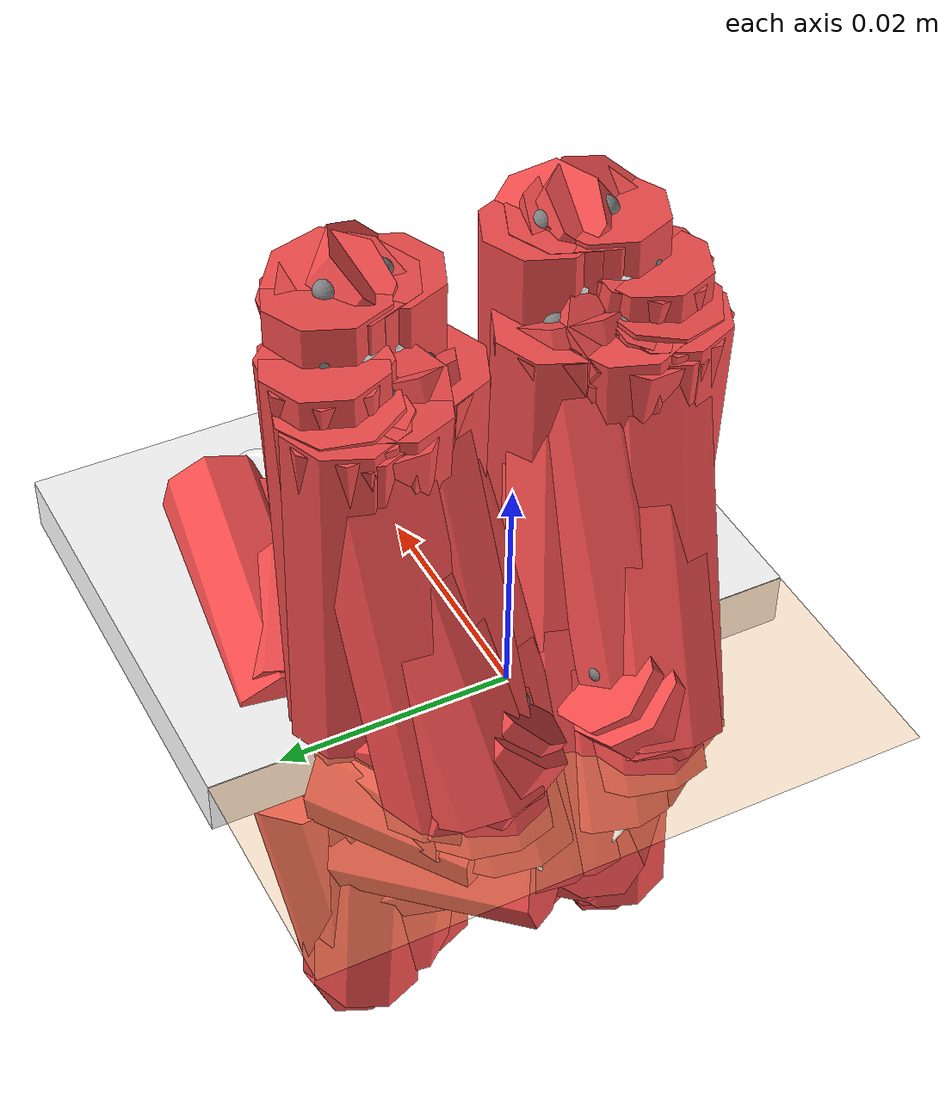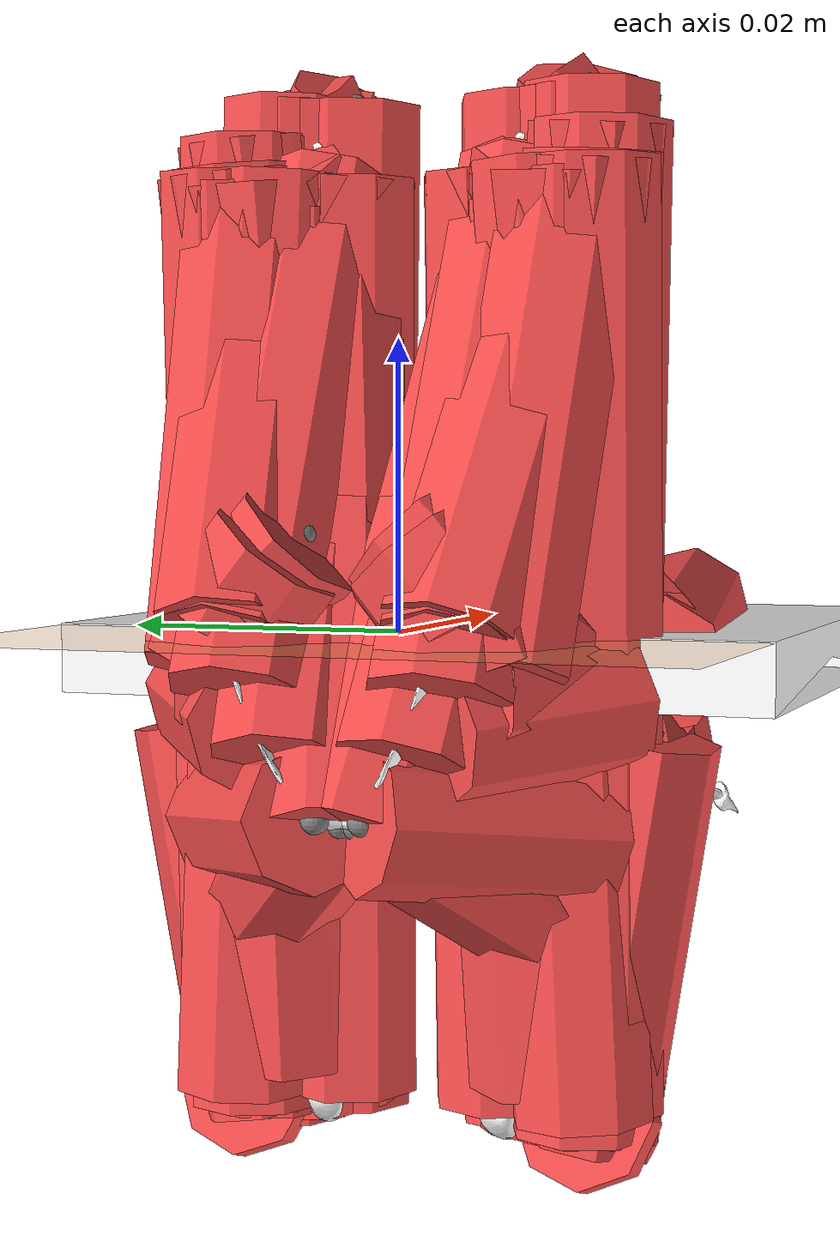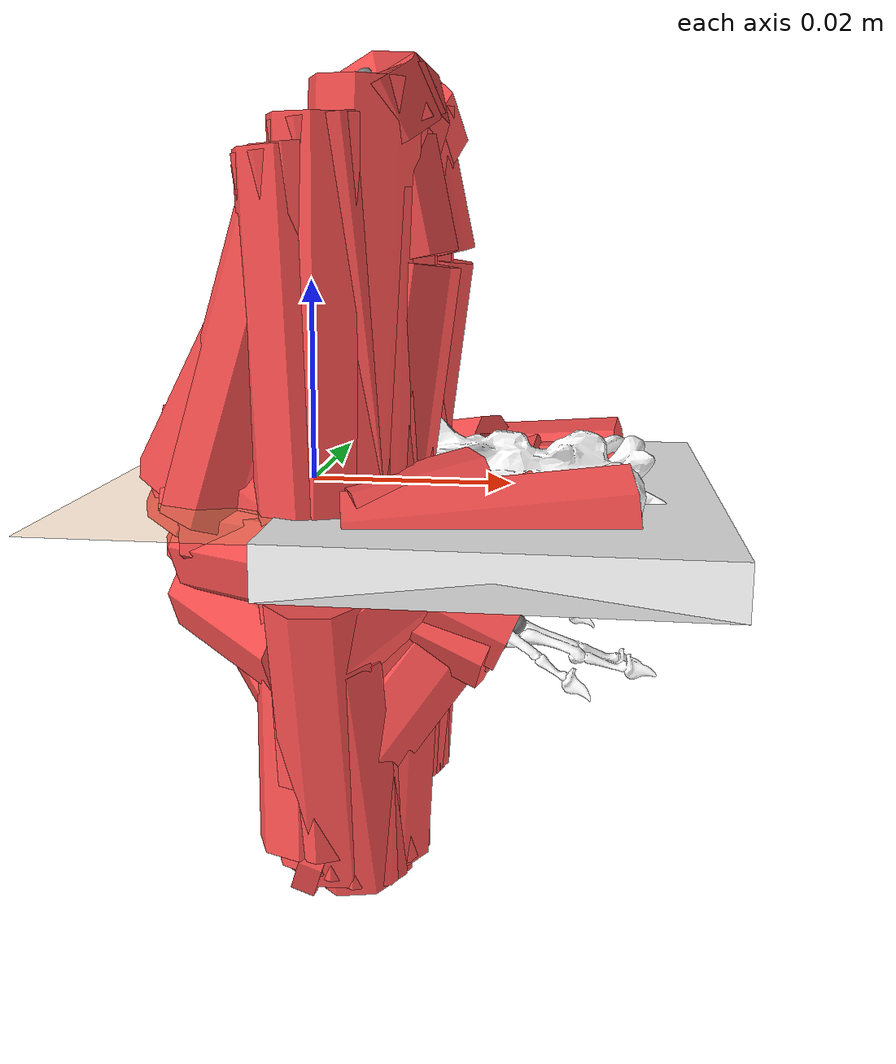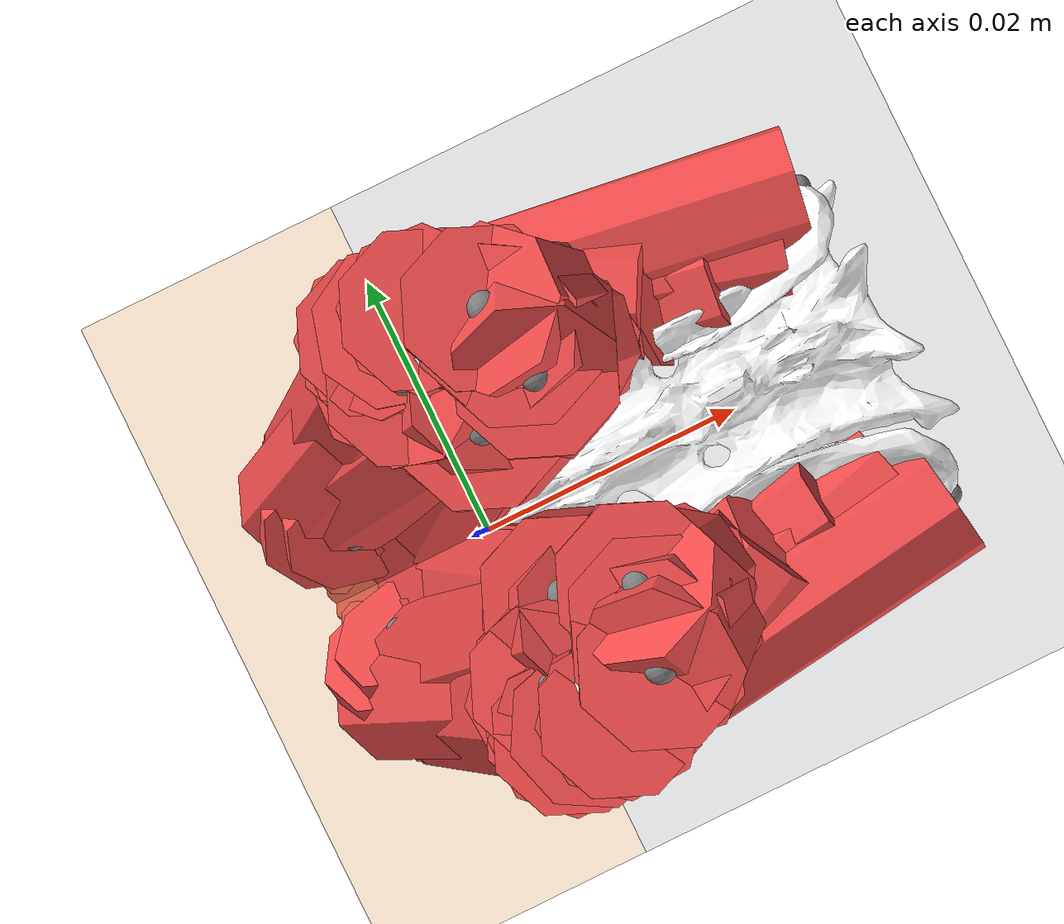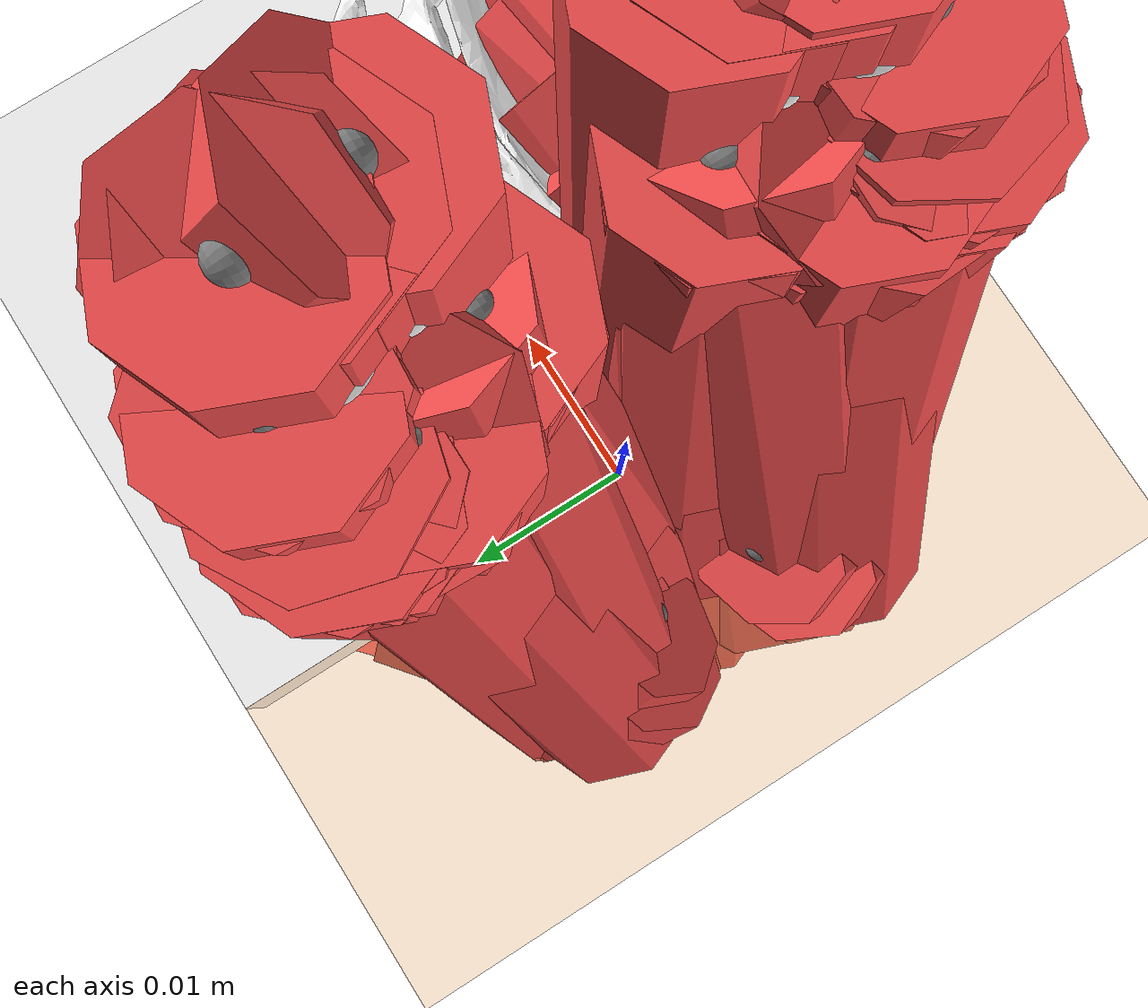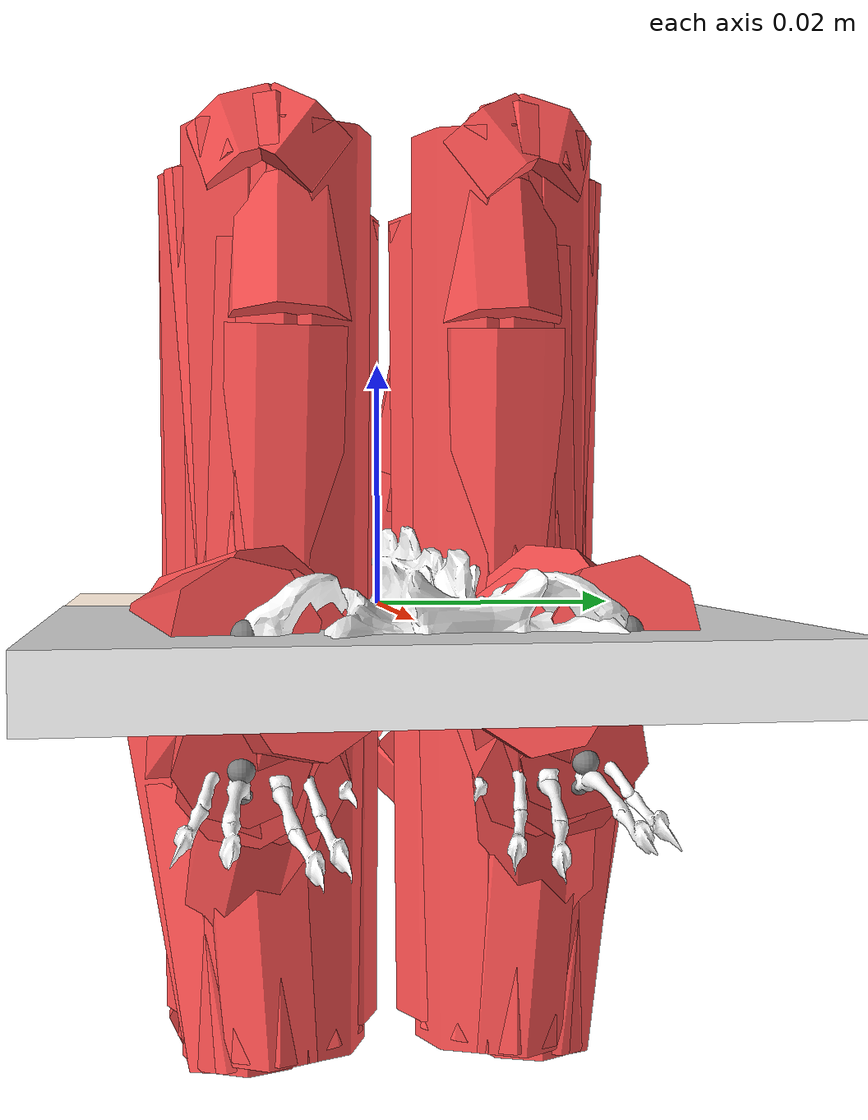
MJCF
<mujoco model="template">
  <!-- This model has been converted from an OpenSim model. Model conversion by MyoConverter https://github.com/MyoHub/myoconverter. This model is licensed under Apache 2.0. -->
  <!-- Credits from the original OpenSim model. Note! If the following has any license information, it applies to the original OpenSim model. Credits: Model authors names.. -->
  <!-- Note: inertiagrouprange="0 1" means that groups 0-1 will be used to infer masses/inertias, and groups 2-5 are
  only for visualisation (e.g. wrapping objects) !-->
  <compiler inertiafromgeom="auto" angle="radian" balanceinertia="true" boundmass="0.001" boundinertia="0.001" inertiagrouprange="0 1">
    <lengthrange inttotal="50" useexisting="true"/>
  </compiler>
  <option collision="predefined"/>
  <visual>
    <scale framelength="0.5" framewidth="0.01"/>
  </visual>
  <default>
    <joint limited="true" damping="0.05" armature="0.00001" stiffness="0"/>
    <geom rgba="0.8 0.6 .4 1" margin="0.001"/>
    <site size="0.001"/>
    <tendon width="0.005" rgba=".95 .3 .3 1" limited="false"/>
    <default class="muscle">
      <muscle ctrllimited="true" ctrlrange="0 1" scale="200"/>
    </default>
    <default class="motor">
      <general gainprm="5 0 0 0 0 0 0 0 0 0"/>
    </default>
  </default>
  <option timestep="0.002"/>
  <!-- nuser_jnt=1, the parameter is used to store default value of the joint, and nkey=1 to store keyframe with
   default joint positions set !-->
  <size njmax="1000" nconmax="400" nuser_jnt="1" nkey="1"/>
  <worldbody>
    <!-- The converter script assumes a body named 'ground' exists as a child element of worldbody -->
    <body name="ground" euler="1.571 0 0">
      <geom name="ground-plane" pos="0 0 0" euler="-1.571 0 0" size="10 10 0.125" type="plane" rgba="1.0 0.7 0.4 1.0" condim="3"/>
      <geom name="ground_geom_1" type="mesh" pos="0 0 0" euler="0 0 0" mesh="ground_geom_1_ground" rgba="1 1 1 1" group="0"/>
    </body>
    <light directional="true"/>
    <body name="spine" pos="0 0 0" euler="1.571 0 0">
      <inertial mass="0.12" pos="0 0 0" fullinertia="4.7999999999999998e-06 4.7999999999999998e-06 4.7999999999999998e-06 0 0 0"/>
      <geom name="spine_geom_1" type="mesh" mesh="spine_geom_1_spine_y2j" rgba="1 1 1 1" group="0"/>
      <joint name="sacrum_x" range="-0.1 0.25" limited="true" user="0.0" ref="0" axis="1 0 0" type="slide" damping="0" stiffness="0"/>
      <joint name="sacrum_y" range="0 0.2" limited="true" user="0.05" ref="0" axis="0 1 0" type="slide" damping="0" stiffness="0"/>
      <joint name="sacrum_z" range="-0.1 0.1" limited="true" user="0.0" ref="0" axis="0 0 1" type="slide" damping="0" stiffness="0"/>
      <joint name="sacrum_pitch" range="-1.571 1.571" limited="true" user="0.52359878" ref="0" axis="0 0 1" type="hinge" damping="0" stiffness="0"/>
      <joint name="sacrum_roll" range="-1.571 1.571" limited="true" user="0.0" ref="0" axis="1 0 0" type="hinge" damping="0" stiffness="0"/>
      <joint name="sacrum_yaw" range="-1.571 1.571" limited="true" user="0.0" ref="0" axis="0 1 0" type="hinge" damping="0" stiffness="0"/>
      <body name="pelvis_r" pos="0.005 -0.003 0.01" euler="-0 0 0">
        <inertial mass="0.02" pos="0 0 0" fullinertia="3.9999999999999998e-06 3.4999999999999999e-06 3.4999999999999999e-06 0 0 0"/>
        <geom name="pelvis_r_geom_1" type="mesh" mesh="pelvis_r_geom_1_pelvis_r_y2j" rgba="1 1 1 1" group="0"/>
        <joint name="sacroiliac_r_flx" range="-0.02301 0.1515" limited="true" user="0.06457718" ref="0" axis="0 0 1" type="hinge"/>
        <body name="femur_r" pos="0 0 0" euler="-0 0 0">
          <inertial mass="0.02" pos="0 -0.014999999999999999 0" fullinertia="1.6199999999999999e-06 2.4999999999999999e-07 1.6199999999999999e-06 0 0 0"/>
          <geom name="femur_r_geom_1" type="mesh" mesh="femur_r_geom_1_femur_r_y2j" rgba="1 1 1 1" group="0"/>
          <joint name="hip_r_flx" range="-0.8727 1.222" limited="true" user="0.6981317" ref="0" axis="0 0 1" type="hinge"/>
          <joint name="hip_r_add" range="-0.8727 0.3491" limited="true" user="-0.17453293" ref="0" axis="1 0 0" type="hinge"/>
          <joint name="hip_r_int" range="-0.8727 0.6981" limited="true" user="0.0" ref="0" axis="0 1 0" type="hinge"/>
          <body name="tibia_r" pos="0 0 0" euler="-0 0 0">
            <inertial mass="0.02" pos="0 0.014999999999999999 0" fullinertia="1.6199999999999999e-06 2.4999999999999999e-07 1.6199999999999999e-06 0 0 0"/>
            <geom name="tibia_r_geom_1" type="mesh" mesh="tibia_r_geom_1_tibia_r_y2j" rgba="1 1 1 1" group="0"/>
            <joint name="knee_r_translation1" range="-0.04232 -0.01539" limited="true" user="-0.03798330700918597" ref="0" axis="1 0 0" type="slide"/>
            <joint name="knee_r_translation2" range="-0.0695 0.00082" limited="true" user="-0.013527600798462602" ref="0" axis="0 1 0" type="slide"/>
            <joint name="knee_r_translation3" range="-0.00371 0.00227" limited="true" user="0.0011682819027788627" ref="0" axis="0 0 1" type="slide"/>
            <joint name="knee_r_flx" range="-2.618 -0.3491" limited="true" user="-2.0943951" ref="0" axis="0 0 1" type="hinge"/>
            <joint name="knee_r_rotation2" range="-0.08727 0.06458" limited="true" user="-0.05238438333586499" ref="0" axis="1 0 0" type="hinge"/>
            <joint name="knee_r_rotation3" range="-2.618 -0.3491" limited="false" user="-2.0943951" ref="0" axis="0 1 0" type="hinge"/>
            <body name="foot_r" pos="0 0 0" euler="-0 0 0">
              <inertial mass="0.02" pos="0.0070000000000000001 -0.0050000000000000001 0" fullinertia="2.4999999999999999e-07 1.6199999999999999e-06 1.6199999999999999e-06 0 0 0"/>
              <geom name="foot_r_geom_1" type="mesh" mesh="foot_r_geom_1_foot_r_y2j" rgba="1 1 1 1" group="0"/>
              <joint name="ankle_r_translation1" range="-1e-06 0" limited="true" user="0.0" ref="0" axis="1 0 0" type="slide"/>
              <joint name="ankle_r_translation2" range="-1e-06 0" limited="true" user="0.0" ref="0" axis="0 1 0" type="slide"/>
              <joint name="ankle_r_translation3" range="-1e-06 0" limited="true" user="0.0" ref="0" axis="0 0 1" type="slide"/>
              <joint name="ankle_r_flx" range="-0.5236 1.047" limited="true" user="0.87266463" ref="0" axis="0 0 1" type="hinge"/>
              <joint name="ankle_r_add" range="-0.08727 0.6109" limited="true" user="-0.08726646" ref="0" axis="1 0 0" type="hinge"/>
              <joint name="ankle_r_int" range="-0.8727 0.2618" limited="true" user="0.0" ref="0" axis="0 1 0" type="hinge"/>
              <site name="R_MG_R_MG_foot_r_via_4" pos="-0.0026293121177333994 -0.00072047123216882733 -0.00065683820638507307"/>
              <site name="R_MG_R_MG_foot_r_insertion_5" pos="-0.0025817433097735146 -0.0018784277993972886 -0.00021392703385158783"/>
              <site name="R_LG_R_LG_foot_r_via_4" pos="-0.0033211822029397763 -0.00075023517133785149 0.00080718803569829027"/>
              <site name="R_LG_R_LG_foot_r_insertion_5" pos="-0.0026415785920760686 -0.0018351687399643841 0.00084233790459717372"/>
              <site name="R_Pla_R_Pla_foot_r_via_4" pos="-0.0032797426462929319 -0.00075768874322020539 0.00037665664305988362"/>
              <site name="R_Pla_R_Pla_foot_r_insertion_5" pos="-0.0029936172679865427 -0.0019607148865995339 0.00023361534915719931"/>
              <site name="R_Sol_R_Sol_foot_r_via_3" pos="-0.0032181046324903169 -0.00076998119487961276 3.9245780893648878e-05"/>
              <site name="R_Sol_R_Sol_foot_r_insertion_4" pos="-0.0029472624548757854 -0.0019339492033808299 -0.00011047423518475194"/>
              <site name="R_TA_R_TA_foot_r_via_4" pos="0.0042194911153077396 -0.0016674218815300468 -0.00042050833941059869"/>
              <site name="R_TA_R_TA_foot_r_insertion_5" pos="0.0065968683046317284 -0.0035871878875917453 -0.00094015276459013218"/>
              <site name="R_EDL_R_EDL_foot_r_via_4" pos="0.0036166791022289712 -0.0018204709676187735 0.0013459398442315458"/>
              <site name="R_EDL_R_EDL_foot_r_insertion_5" pos="0.016179517129514525 -0.0073794326491467034 0.0024144421845933035"/>
              <site name="R_TP_R_TP_foot_r_via_3" pos="-0.0033400078438677633 -0.00078904603140427594 -0.00060001444353816632"/>
              <site name="R_TP_R_TP_foot_r_via_4" pos="-0.0010131167230638014 -0.0026205678489572598 -0.00035907929866081417"/>
              <site name="R_TP_R_TP_foot_r_insertion_5" pos="0.0034668092366839632 -0.0039292543334018956 -0.0012423067520079456"/>
              <site name="R_FDL_R_FDL_foot_r_via_3" pos="-0.0032361789644938864 -0.00076090741262724272 -0.00034919280568167232"/>
              <site name="R_FDL_R_FDL_foot_r_via_4" pos="-0.0012602423018097397 -0.0023322913727976458 -0.00012500786501590339"/>
              <site name="R_FDL_R_FDL_foot_r_via_5" pos="0.0014779958815920383 -0.0039188251353921592 -0.0003360476824415486"/>
              <site name="R_FDL_R_FDL_foot_r_insertion_6" pos="0.014730129608683721 -0.00907331782803515 0.0022770879247078495"/>
              <site name="R_FHL_R_FHL_foot_r_via_3" pos="-0.0029465141563377508 -0.00090030480881909101 -0.00069383134009496934"/>
              <site name="R_FHL_R_FHL_foot_r_via_4" pos="-0.00093842961382891734 -0.0025362026176933001 -0.00080272868574339539"/>
              <site name="R_FHL_R_FHL_foot_r_via_5" pos="0.0022199370243366047 -0.0040660538648974948 -0.00050577732889629671"/>
              <site name="R_FHL_R_FHL_foot_r_insertion_6" pos="0.015040568824663108 -0.0086881797439026433 -0.0004912041726219704"/>
              <site name="R_Per_R_Per_foot_r_via_3" pos="-0.0029552478015951841 -0.00083796282491848284 0.001232001667022401"/>
              <site name="R_Per_R_Per_foot_r_via_4" pos="-0.00081017195968501325 -0.0024675233623070768 0.0015153969925863636"/>
              <site name="R_Per_R_Per_foot_r_via_5" pos="0.0015129544379533281 -0.0039183788633522822 0.001889846079610763"/>
              <site name="R_Per_R_Per_foot_r_insertion_6" pos="0.0044874837699264789 -0.0050531654380788797 0.0008720614870825796"/>
              <site name="R_Toe_marker" group="4" pos="0.015 -0.005 0.005" rgba="1 0.1 0.5 0.5" size="0.01"/>
            </body>
            <site name="R_BFa_R_BFa_tibia_r_insertion_4" pos="-0.003484530813625489 0.032011678324168735 0.0015299297737748447"/>
            <site name="R_BFp_R_BFp_tibia_r_via_2" pos="-0.0036557684352398691 0.026290265029329133 0.00057941086931954445"/>
            <site name="R_BFp_R_BFp_tibia_r_insertion_3" pos="0.0020302880603587561 0.02689894346892371 0.00012878364389428147"/>
            <site name="R_STp_R_STp_tibia_r_insertion_2" pos="0.0019545104279559676 0.027158576818076274 -0.0022004333936168938"/>
            <site name="R_STa_R_STa_tibia_r_insertion_4" pos="0.0019545104279559676 0.027158576818076274 -0.0022004333936168938"/>
            <site name="R_SM_R_SM_tibia_r_insertion_2" pos="0.00013428264422099187 0.034067777580700627 -0.0026748706066116812"/>
            <site name="R_GP_R_GP_tibia_r_insertion_2" pos="0.00191207714288815 0.028044889519162099 -0.002940728904990266"/>
            <site name="R_GA_R_GA_tibia_r_insertion_2" pos="0.0013462506595494296 0.030542531838635818 -0.0028833213808457077"/>
            <site name="R_AM_R_AM_tibia_r_insertion_2" pos="0.00059705672610007253 0.032246150364863731 -0.002761479960466294"/>
            <site name="R_RF_R_RF_tibia_r_via_3" pos="0.0032390608861469104 0.040081646109172385 -0.0013843053100119978"/>
            <site name="R_VL_R_VL_tibia_r_via_3" pos="0.0024723984324934692 0.040377007110372426 0.0012539964178194629"/>
            <site name="R_VL_R_VL_tibia_r_insertion_4" pos="0.004718857433953132 0.03562576272853904 -0.00021923204243533403"/>
            <site name="R_VI_R_VI_tibia_r_via_3" pos="0.0027595296183368233 0.04009332964598028 -8.171980371359956e-05"/>
            <site name="R_VI_R_VI_tibia_r_insertion_4" pos="0.004718857433953132 0.03562576272853904 -0.00021923204243533403"/>
            <site name="R_VM_R_VM_tibia_r_via_3" pos="0.0034208328708271707 0.039982363648705554 -0.0034243409868106459"/>
            <site name="R_VM_R_VM_tibia_r_insertion_4" pos="0.004718857433953132 0.03562576272853904 -0.00021923204243533403"/>
            <site name="R_MG_R_MG_tibia_r_via_2" pos="-0.0010695512631639771 0.034324860237913049 -0.0046069947557144091"/>
            <site name="R_MG_R_MG_tibia_r_via_3" pos="-0.00017208968310084092 -7.220748889143723e-05 -0.0022713069343530353"/>
            <site name="R_LG_R_LG_tibia_r_via_2" pos="-0.004058510709898204 0.034777316547928629 0.0030711960798243928"/>
            <site name="R_LG_R_LG_tibia_r_via_3" pos="-0.00054474982200915754 0.00062243478708937875 0.00071155456277632368"/>
            <site name="R_Pla_R_Pla_tibia_r_via_2" pos="-0.0042159218093283483 0.033942539584827049 0.0023087107628135353"/>
            <site name="R_Pla_R_Pla_tibia_r_via_3" pos="-0.00052200571923873441 0.00062453411887466309 0.00028895133021098461"/>
            <site name="R_Sol_R_Sol_tibia_r_origin_1" pos="-0.0044245928352569129 0.034024163811523053 0.00053919207551161158"/>
            <site name="R_Sol_R_Sol_tibia_r_via_2" pos="-0.00048786457156357182 0.00062768542351059574 -0.00034541791779368902"/>
            <site name="R_TA_R_TA_tibia_r_origin_1" pos="0.0035505386978079987 0.035037748924045174 -0.0019440528311649135"/>
            <site name="R_TA_R_TA_tibia_r_via_2" pos="0.0056470213478842573 0.025046797070804174 -0.0017057292161844061"/>
            <site name="R_TA_R_TA_tibia_r_via_3" pos="0.0027596960087074279 0.0023377313270555459 -0.0013321208788449126"/>
            <site name="R_EDL_R_EDL_tibia_r_via_2" pos="-0.00092163439046292605 0.037397473459058868 0.0030732539940742576"/>
            <site name="R_EDL_R_EDL_tibia_r_via_3" pos="0.0025206926712775584 0.0021270811564358142 0.00056636284519840101"/>
            <site name="R_TP_R_TP_tibia_r_origin_1" pos="-0.0023345420240780098 0.032236371135882125 -0.0014540368166148113"/>
            <site name="R_TP_R_TP_tibia_r_via_2" pos="-0.00028222161798801323 6.8588657527313048e-05 -0.0016216821321764438"/>
            <site name="R_FDL_R_FDL_tibia_r_origin_1" pos="-0.0026840614529671609 0.03409518707458916 -0.00078640487773796899"/>
            <site name="R_FDL_R_FDL_tibia_r_via_2" pos="-0.00017087065298149358 0.00053796290013336748 -0.0012230543435641488"/>
            <site name="R_FHL_R_FHL_tibia_r_origin_1" pos="-0.001068666539370352 0.032006819684307498 -0.0013870489299196373"/>
            <site name="R_FHL_R_FHL_tibia_r_via_2" pos="-0.00027160509753900407 0.00038497685398606847 -0.0019902806375314643"/>
            <site name="R_Per_R_Per_tibia_r_origin_1" pos="-0.002845861606499855 0.035260074590016774 0.0031146385568358447"/>
            <site name="R_Per_R_Per_tibia_r_via_2" pos="-0.0005653444821001781 0.00062053385369259355 0.0010942194678684547"/>
            <site name="R_Pop_R_Pop_tibia_r_via_3" pos="-0.0038628412246485676 0.034601071475264512 -0.00033593283243615613"/>
            <site name="R_Pop_R_Pop_tibia_r_insertion_4" pos="0.0018917936421075621 0.025146549340901669 -0.0023647085979182189"/>
            <site name="R_Ankle_marker" group="4" pos="0 0 0.004" rgba="1 0.1 0.5 0.5" size="0.01"/>
          </body>
          <site name="R_CF_R_CF_femur_r_insertion_4" pos="-0.0022684254389458321 -0.027910269443086222 -0.00061842400435038758"/>
          <site name="R_QF_R_QF_femur_r_insertion_2" pos="-0.0031357171473441604 -0.0015417498896185199 0.0049028923678654888"/>
          <site name="R_TFL_R_TFL_femur_r_insertion_2" pos="0.0011164950559486462 -0.02060285298813587 0.002134524834841508"/>
          <site name="R_GMa_R_GMa_femur_r_insertion_2" pos="-0.001317571917434045 -0.0088828732513830388 0.0058215690361145189"/>
          <site name="R_GMe_R_GMe_femur_r_insertion_2" pos="0.0012369429192032478 0.00062053221140443847 0.0063923431755444219"/>
          <site name="R_GMi_R_GMi_femur_r_insertion_2" pos="0.0013541506891032549 -0.00039531434587411604 0.0057030129702259512"/>
          <site name="R_Pir_R_Pir_femur_r_insertion_2" pos="0.0017706739814439172 0.0012493883100604425 0.0057670339801603829"/>
          <site name="R_AL_R_AL_femur_r_insertion_2" pos="-0.0019918213886055722 -0.015377865000054718 0.0015189079507442176"/>
          <site name="R_AB_R_AB_femur_r_insertion_2" pos="-0.002057502010430385 -0.017378831884309696 0.0019348686634569879"/>
          <site name="R_Pec_R_Pec_femur_r_insertion_2" pos="-0.003126830489249827 -0.010531390797443894 0.0034782321899123839"/>
          <site name="R_IP_R_IP_femur_r_insertion_2" pos="-0.00025659756247026861 -0.0044220286710901658 0.001600474652992121"/>
          <site name="R_OE_R_OE_femur_r_insertion_2" pos="-0.001946152258881754 -0.0015154683655583686 0.0016713661995924997"/>
          <site name="R_OI_R_OI_femur_r_via_2" pos="-0.00095512489578496119 -0.00018123994479910031 0.0032942430230493936"/>
          <site name="R_GS_R_GS_femur_r_insertion_2" pos="-3.5038101435218852e-05 -0.0063606644370297546 0.0023669521479270784"/>
          <site name="R_GI_R_GI_femur_r_insertion_2" pos="-0.001800937985408888 -0.00040948339558884568 0.0019596297721057739"/>
          <site name="R_RF_R_RF_femur_r_via_2" pos="0.0030684580308198506 -0.03191590274652506 -0.00069033848925471571"/>
          <site name="R_VL_R_VL_femur_r_origin_1" pos="-0.00127120986424196 -0.0039932876287063733 0.006780542782365259"/>
          <site name="R_VL_R_VL_femur_r_via_2" pos="-0.00044582030953245694 -0.032066259819236415 0.0020790951836017046"/>
          <site name="R_VI_R_VI_femur_r_origin_1" pos="-0.00045543934104507649 -0.010389782302747223 0.0050254953444121087"/>
          <site name="R_VI_R_VI_femur_r_via_2" pos="0.001594776247714075 -0.033020882181012845 0.0017173522086202124"/>
          <site name="R_VM_R_VM_femur_r_origin_1" pos="-0.00025295229886874429 -0.0053315215686960517 0.0017116838020910076"/>
          <site name="R_VM_R_VM_femur_r_via_2" pos="0.0023274210477247348 -0.031900245519552624 -0.0028887450690516419"/>
          <site name="R_MG_R_MG_femur_r_origin_1" pos="0.0003887868176004174 -0.03033571843216526 -0.0041750224875530366"/>
          <site name="R_LG_R_LG_femur_r_origin_1" pos="-0.001531530670924563 -0.029781540132054404 0.0029727122929873485"/>
          <site name="R_Pla_R_Pla_femur_r_origin_1" pos="-0.0014997187920991885 -0.028939379877426438 0.0023585913062059288"/>
          <site name="R_EDL_R_EDL_femur_r_origin_1" pos="-0.0017516296033354179 -0.031464266695940039 0.0021799439031973218"/>
          <site name="R_Pop_R_Pop_femur_r_origin_1" pos="-0.0010187702989538404 -0.030813563282131601 0.0027711015910455231"/>
          <site name="R_Pop_R_Pop_femur_r_via_2" pos="-0.0032207882412246046 -0.030078174947695314 0.0027004288919401289"/>
          <site name="R_Knee_marker" group="4" pos="0 -0.035 0" rgba="1 0.1 0.5 0.5" size="0.01"/>
        </body>
        <site name="R_BFa_R_BFa_pelvis_r_origin_1" pos="-0.013229717820511223 0.0098054905408808749 -0.0063165953521168872"/>
        <site name="R_BFa_R_BFa_pelvis_r_via_2" pos="-0.013378774666965522 0.0053473859774945233 -0.0017075405822901592"/>
        <site name="R_BFa_R_BFa_pelvis_r_via_3" pos="-0.013413589043210255 0.001267500059252866 -0.00019529884968006892"/>
        <site name="R_BFp_R_BFp_pelvis_r_origin_1" pos="-0.016162235231798133 0.0037023387696135533 -0.0022577101403499565"/>
        <site name="R_CF_R_CF_pelvis_r_origin_1" pos="-0.0076772753262189034 0.010075307296014163 -0.0060885087392919439"/>
        <site name="R_CF_R_CF_pelvis_r_via_2" pos="-0.007116509318988844 0.0055297488032940061 -0.0027397400659646479"/>
        <site name="R_CF_R_CF_pelvis_r_via_3" pos="-0.0059940150798956414 0.0012037357031758399 -0.0011243740210735956"/>
        <site name="R_STp_R_STp_pelvis_r_origin_1" pos="-0.015920977612210382 0.0026513939647869454 -0.0023545170186918775"/>
        <site name="R_STa_R_STa_pelvis_r_origin_1" pos="-0.014670766549866902 0.00908058085975081 -0.0054268169454483976"/>
        <site name="R_STa_R_STa_pelvis_r_via_2" pos="-0.01465662768421324 0.0059921366564091652 -0.0028941923462869031"/>
        <site name="R_STa_R_STa_pelvis_r_via_3" pos="-0.014665527575582774 0.0039098160227850213 -0.0017348347410472585"/>
        <site name="R_SM_R_SM_pelvis_r_origin_1" pos="-0.015923433335334969 -0.00040186220959461316 -0.0031049562628849251"/>
        <site name="R_QF_R_QF_pelvis_r_origin_1" pos="-0.014310933941641533 -0.0027202676206083908 -0.0038766923407194203"/>
        <site name="R_TFL_R_TFL_pelvis_r_origin_1" pos="0.016498116236553562 0.00094155006633434056 -0.0014876100538054068"/>
        <site name="R_GMa_R_GMa_pelvis_r_origin_1" pos="0.014401871761942683 0.0028336429749137391 -0.0010371846959494695"/>
        <site name="R_GMe_R_GMe_pelvis_r_origin_1" pos="0.026229057176819233 0.0029827200642929142 0.0024358302967715352"/>
        <site name="R_GMi_R_GMi_pelvis_r_origin_1" pos="0.02369672999842579 0.001357483024595151 -0.0004103219425995821"/>
        <site name="R_Pir_R_Pir_pelvis_r_origin_1" pos="0.012864775127775714 0.003610721478830591 4.0150212846544941e-05"/>
        <site name="R_GP_R_GP_pelvis_r_origin_1" pos="-0.015030581294219525 -0.0049000440937163473 -0.0056940706080489487"/>
        <site name="R_GA_R_GA_pelvis_r_origin_1" pos="-0.014375403174611719 -0.0090359807962863744 -0.0092668353018262126"/>
        <site name="R_AL_R_AL_pelvis_r_origin_1" pos="-0.0049282065931665975 -0.0059007554825905723 -0.0061948646210370157"/>
        <site name="R_AM_R_AM_pelvis_r_origin_1" pos="-0.013020897286129544 -0.0090734148585075482 -0.0092643609873389599"/>
        <site name="R_AB_R_AB_pelvis_r_origin_1" pos="-0.012420918719149444 -0.0079870458646932405 -0.0085412318945423445"/>
        <site name="R_Pec_R_Pec_pelvis_r_origin_1" pos="-0.015875502409913686 -0.0084737303141124692 -0.0083246640285783539"/>
        <site name="R_IP_R_IP_pelvis_r_origin_1" pos="0.021757875300470308 -0.0010771044273091184 -0.0021378421050556682"/>
        <site name="R_OE_R_OE_pelvis_r_origin_1" pos="-0.009777414659020706 -0.0017475090585732473 -0.0034964219098101755"/>
        <site name="R_OI_R_OI_pelvis_r_origin_1" pos="-0.013774326031796418 -0.00025582021444934882 -0.0024161510110617583"/>
        <site name="R_GS_R_GS_pelvis_r_origin_1" pos="0.0190570240163879 0.0018477539321075332 -0.0010365239965345805"/>
        <site name="R_GI_R_GI_pelvis_r_origin_1" pos="-0.012418637368222133 0.0057219723744547108 -0.0029806125298927236"/>
        <site name="R_RF_R_RF_pelvis_r_origin_1" pos="0.0047952754089115729 -0.00043225635404777992 0.0013414411745775686"/>
        <site name="R_Iliac_Crest_marker" group="4" pos="0.028 0.004 0.01" rgba="1 0.1 0.5 0.5" size="0.01"/>
        <site name="R_Hip_marker" group="4" pos="-0.005 0.005 0.01" rgba="1 0.1 0.5 0.5" size="0.01"/>
      </body>
      <body name="pelvis_l" pos="0.005 -0.003 -0.01" euler="-0 0 0">
        <inertial mass="0.02" pos="0 0 0" fullinertia="3.9999999999999998e-06 3.4999999999999999e-06 3.4999999999999999e-06 0 0 0"/>
        <geom name="pelvis_l_geom_1" type="mesh" mesh="pelvis_l_geom_1_pelvis_r_y2j" rgba="1 1 1 1" group="0"/>
        <joint name="sacroiliac_l_flx" range="-0.02301 0.1515" limited="true" user="0.06457718" ref="0" axis="0 0 1" type="hinge"/>
        <body name="femur_l" pos="0 0 0" euler="-0 0 0">
          <inertial mass="0.02" pos="0 -0.014999999999999999 0" fullinertia="1.6199999999999999e-06 2.4999999999999999e-07 1.6199999999999999e-06 0 0 0"/>
          <geom name="femur_l_geom_1" type="mesh" mesh="femur_l_geom_1_femur_r_y2j" rgba="1 1 1 1" group="0"/>
          <joint name="hip_l_flx" range="-0.8727 1.222" limited="true" user="0.6981317" ref="0" axis="0 0 1" type="hinge"/>
          <joint name="hip_l_add" range="-0.8727 0.3491" limited="true" user="0.17453293" ref="0" axis="-1 -0 -0" type="hinge"/>
          <joint name="hip_l_int" range="-0.8727 0.6981" limited="true" user="-0.0" ref="0" axis="-0 -1 -0" type="hinge"/>
          <body name="tibia_l" pos="0 0 0" euler="-0 0 0">
            <inertial mass="0.02" pos="0 0.014999999999999999 0" fullinertia="1.6199999999999999e-06 2.4999999999999999e-07 1.6199999999999999e-06 0 0 0"/>
            <geom name="tibia_l_geom_1" type="mesh" mesh="tibia_l_geom_1_tibia_r_y2j" rgba="1 1 1 1" group="0"/>
            <joint name="knee_l_translation1" range="-0.04232 -0.01539" limited="true" user="-0.03798330700918597" ref="0" axis="1 0 0" type="slide"/>
            <joint name="knee_l_translation2" range="-0.0695 0.00082" limited="true" user="-0.013527600798462602" ref="0" axis="0 1 0" type="slide"/>
            <joint name="knee_l_translation3" range="-0.00227 0.00371" limited="true" user="-0.0011682819027788627" ref="0" axis="0 0 1" type="slide"/>
            <joint name="knee_l_flx" range="-2.618 -0.3491" limited="true" user="-2.0943951" ref="0" axis="0 0 1" type="hinge"/>
            <joint name="knee_l_rotation2" range="-0.06458 0.08727" limited="true" user="0.05238438333586499" ref="0" axis="1 0 0" type="hinge"/>
            <joint name="knee_l_rotation3" range="-2.618 -0.3491" limited="false" user="-2.0943951" ref="0" axis="0 1 0" type="hinge"/>
            <body name="foot_l" pos="0 0 0" euler="-0 0 0">
              <inertial mass="0.02" pos="0.0070000000000000001 -0.0050000000000000001 0" fullinertia="2.4999999999999999e-07 1.6199999999999999e-06 1.6199999999999999e-06 0 0 0"/>
              <geom name="foot_l_geom_1" type="mesh" mesh="foot_l_geom_1_foot_r_y2j" rgba="1 1 1 1" group="0"/>
              <joint name="ankle_l_translation1" range="-1e-06 0" limited="true" user="0.0" ref="0" axis="1 0 0" type="slide"/>
              <joint name="ankle_l_translation2" range="-1e-06 0" limited="true" user="0.0" ref="0" axis="0 1 0" type="slide"/>
              <joint name="ankle_l_translation3" range="-1e-06 0" limited="true" user="0.0" ref="0" axis="0 0 1" type="slide"/>
              <joint name="ankle_l_flx" range="-0.5236 1.047" limited="true" user="0.87266463" ref="0" axis="0 0 1" type="hinge"/>
              <joint name="ankle_l_add" range="-0.08727 0.6109" limited="true" user="0.08726646" ref="0" axis="-1 -0 -0" type="hinge"/>
              <joint name="ankle_l_int" range="-0.8727 0.2618" limited="true" user="-0.0" ref="0" axis="-0 -1 -0" type="hinge"/>
              <site name="L_MG_L_MG_foot_l_via_4" pos="-0.0026293121177333994 -0.00072047123216882733 0.00065683820638507307"/>
              <site name="L_MG_L_MG_foot_l_insertion_5" pos="-0.0025817433097735146 -0.0018784277993972886 0.00021392703385158783"/>
              <site name="L_LG_L_LG_foot_l_via_4" pos="-0.0033211822029397763 -0.00075023517133785149 -0.00080718803569829027"/>
              <site name="L_LG_L_LG_foot_l_insertion_5" pos="-0.0026415785920760686 -0.0018351687399643841 -0.00084233790459717372"/>
              <site name="L_Pla_L_Pla_foot_l_via_4" pos="-0.0032797426462929319 -0.00075768874322020539 -0.00037665664305988362"/>
              <site name="L_Pla_L_Pla_foot_l_insertion_5" pos="-0.0029936172679865427 -0.0019607148865995339 -0.00023361534915719931"/>
              <site name="L_Sol_L_Sol_foot_l_via_3" pos="-0.0032181046324903169 -0.00076998119487961276 -3.9245780893648878e-05"/>
              <site name="L_Sol_L_Sol_foot_l_insertion_4" pos="-0.0029472624548757854 -0.0019339492033808299 0.00011047423518475194"/>
              <site name="L_TA_L_TA_foot_l_via_4" pos="0.0042194911153077396 -0.0016674218815300468 0.00042050833941059869"/>
              <site name="L_TA_L_TA_foot_l_insertion_5" pos="0.0065968683046317284 -0.0035871878875917453 0.00094015276459013218"/>
              <site name="L_EDL_L_EDL_foot_l_via_4" pos="0.0036166791022289712 -0.0018204709676187735 -0.0013459398442315458"/>
              <site name="L_EDL_L_EDL_foot_l_insertion_5" pos="0.016179517129514525 -0.0073794326491467034 -0.0024144421845933035"/>
              <site name="L_TP_L_TP_foot_l_via_3" pos="-0.0033400078438677633 -0.00078904603140427594 0.00060001444353816632"/>
              <site name="L_TP_L_TP_foot_l_via_4" pos="-0.0010131167230638014 -0.0026205678489572598 0.00035907929866081417"/>
              <site name="L_TP_L_TP_foot_l_insertion_5" pos="0.0034668092366839632 -0.0039292543334018956 0.0012423067520079456"/>
              <site name="L_FDL_L_FDL_foot_l_via_3" pos="-0.0032361789644938864 -0.00076090741262724272 0.00034919280568167232"/>
              <site name="L_FDL_L_FDL_foot_l_via_4" pos="-0.0012602423018097397 -0.0023322913727976458 0.00012500786501590339"/>
              <site name="L_FDL_L_FDL_foot_l_via_5" pos="0.0014779958815920383 -0.0039188251353921592 0.0003360476824415486"/>
              <site name="L_FDL_L_FDL_foot_l_insertion_6" pos="0.014730129608683721 -0.00907331782803515 -0.0022770879247078495"/>
              <site name="L_FHL_L_FHL_foot_l_via_3" pos="-0.0029465141563377508 -0.00090030480881909101 0.00069383134009496934"/>
              <site name="L_FHL_L_FHL_foot_l_via_4" pos="-0.00093842961382891734 -0.0025362026176933001 0.00080272868574339539"/>
              <site name="L_FHL_L_FHL_foot_l_via_5" pos="0.0022199370243366047 -0.0040660538648974948 0.00050577732889629671"/>
              <site name="L_FHL_L_FHL_foot_l_insertion_6" pos="0.015040568824663108 -0.0086881797439026433 0.0004912041726219704"/>
              <site name="L_Per_L_Per_foot_l_via_3" pos="-0.0029552478015951841 -0.00083796282491848284 -0.001232001667022401"/>
              <site name="L_Per_L_Per_foot_l_via_4" pos="-0.00081017195968501325 -0.0024675233623070768 -0.0015153969925863636"/>
              <site name="L_Per_L_Per_foot_l_via_5" pos="0.0015129544379533281 -0.0039183788633522822 -0.001889846079610763"/>
              <site name="L_Per_L_Per_foot_l_insertion_6" pos="0.0044874837699264789 -0.0050531654380788797 -0.0008720614870825796"/>
            </body>
            <site name="L_BFa_L_BFa_tibia_l_insertion_4" pos="-0.003484530813625489 0.032011678324168735 -0.0015299297737748447"/>
            <site name="L_BFp_L_BFp_tibia_l_via_2" pos="-0.0036557684352398691 0.026290265029329133 -0.00057941086931954445"/>
            <site name="L_BFp_L_BFp_tibia_l_insertion_3" pos="0.0020302880603587561 0.02689894346892371 -0.00012878364389428147"/>
            <site name="L_STp_L_STp_tibia_l_insertion_2" pos="0.0019545104279559676 0.027158576818076274 0.0022004333936168938"/>
            <site name="L_STa_L_STa_tibia_l_insertion_4" pos="0.0019545104279559676 0.027158576818076274 0.0022004333936168938"/>
            <site name="L_SM_L_SM_tibia_l_insertion_2" pos="0.00013428264422099187 0.034067777580700627 0.0026748706066116812"/>
            <site name="L_GP_L_GP_tibia_l_insertion_2" pos="0.00191207714288815 0.028044889519162099 0.002940728904990266"/>
            <site name="L_GA_L_GA_tibia_l_insertion_2" pos="0.0013462506595494296 0.030542531838635818 0.0028833213808457077"/>
            <site name="L_AM_L_AM_tibia_l_insertion_2" pos="0.00059705672610007253 0.032246150364863731 0.002761479960466294"/>
            <site name="L_RF_L_RF_tibia_l_via_3" pos="0.0032390608861469104 0.040081646109172385 0.0013843053100119978"/>
            <site name="L_VL_L_VL_tibia_l_via_3" pos="0.0024723984324934692 0.040377007110372426 -0.0012539964178194629"/>
            <site name="L_VL_L_VL_tibia_l_insertion_4" pos="0.004718857433953132 0.03562576272853904 0.00021923204243533403"/>
            <site name="L_VI_L_VI_tibia_l_via_3" pos="0.0027595296183368233 0.04009332964598028 8.171980371359956e-05"/>
            <site name="L_VI_L_VI_tibia_l_insertion_4" pos="0.004718857433953132 0.03562576272853904 0.00021923204243533403"/>
            <site name="L_VM_L_VM_tibia_l_via_3" pos="0.0034208328708271707 0.039982363648705554 0.0034243409868106459"/>
            <site name="L_VM_L_VM_tibia_l_insertion_4" pos="0.004718857433953132 0.03562576272853904 0.00021923204243533403"/>
            <site name="L_MG_L_MG_tibia_l_via_2" pos="-0.0010695512631639771 0.034324860237913049 0.0046069947557144091"/>
            <site name="L_MG_L_MG_tibia_l_via_3" pos="-0.00017208968310084092 -7.220748889143723e-05 0.0022713069343530353"/>
            <site name="L_LG_L_LG_tibia_l_via_2" pos="-0.004058510709898204 0.034777316547928629 -0.0030711960798243928"/>
            <site name="L_LG_L_LG_tibia_l_via_3" pos="-0.00054474982200915754 0.00062243478708937875 -0.00071155456277632368"/>
            <site name="L_Pla_L_Pla_tibia_l_via_2" pos="-0.0042159218093283483 0.033942539584827049 -0.0023087107628135353"/>
            <site name="L_Pla_L_Pla_tibia_l_via_3" pos="-0.00052200571923873441 0.00062453411887466309 -0.00028895133021098461"/>
            <site name="L_Sol_L_Sol_tibia_l_origin_1" pos="-0.0044245928352569129 0.034024163811523053 -0.00053919207551161158"/>
            <site name="L_Sol_L_Sol_tibia_l_via_2" pos="-0.00048786457156357182 0.00062768542351059574 0.00034541791779368902"/>
            <site name="L_TA_L_TA_tibia_l_origin_1" pos="0.0035505386978079987 0.035037748924045174 0.0019440528311649135"/>
            <site name="L_TA_L_TA_tibia_l_via_2" pos="0.0056470213478842573 0.025046797070804174 0.0017057292161844061"/>
            <site name="L_TA_L_TA_tibia_l_via_3" pos="0.0027596960087074279 0.0023377313270555459 0.0013321208788449126"/>
            <site name="L_EDL_L_EDL_tibia_l_via_2" pos="-0.00092163439046292605 0.037397473459058868 -0.0030732539940742576"/>
            <site name="L_EDL_L_EDL_tibia_l_via_3" pos="0.0025206926712775584 0.0021270811564358142 -0.00056636284519840101"/>
            <site name="L_TP_L_TP_tibia_l_origin_1" pos="-0.0023345420240780098 0.032236371135882125 0.0014540368166148113"/>
            <site name="L_TP_L_TP_tibia_l_via_2" pos="-0.00028222161798801323 6.8588657527313048e-05 0.0016216821321764438"/>
            <site name="L_FDL_L_FDL_tibia_l_origin_1" pos="-0.0026840614529671609 0.03409518707458916 0.00078640487773796899"/>
            <site name="L_FDL_L_FDL_tibia_l_via_2" pos="-0.00017087065298149358 0.00053796290013336748 0.0012230543435641488"/>
            <site name="L_FHL_L_FHL_tibia_l_origin_1" pos="-0.001068666539370352 0.032006819684307498 0.0013870489299196373"/>
            <site name="L_FHL_L_FHL_tibia_l_via_2" pos="-0.00027160509753900407 0.00038497685398606847 0.0019902806375314643"/>
            <site name="L_Per_L_Per_tibia_l_origin_1" pos="-0.002845861606499855 0.035260074590016774 -0.0031146385568358447"/>
            <site name="L_Per_L_Per_tibia_l_via_2" pos="-0.0005653444821001781 0.00062053385369259355 -0.0010942194678684547"/>
            <site name="L_Pop_L_Pop_tibia_l_via_3" pos="-0.0038628412246485676 0.034601071475264512 0.00033593283243615613"/>
            <site name="L_Pop_L_Pop_tibia_l_insertion_4" pos="0.0018917936421075621 0.025146549340901669 0.0023647085979182189"/>
          </body>
          <site name="L_CF_L_CF_femur_l_insertion_4" pos="-0.0022684254389458321 -0.027910269443086222 0.00061842400435038758"/>
          <site name="L_QF_L_QF_femur_l_insertion_2" pos="-0.0031357171473441604 -0.0015417498896185199 -0.0049028923678654888"/>
          <site name="L_TFL_L_TFL_femur_l_insertion_2" pos="0.0011164950559486462 -0.02060285298813587 -0.002134524834841508"/>
          <site name="L_GMa_L_GMa_femur_l_insertion_2" pos="-0.001317571917434045 -0.0088828732513830388 -0.0058215690361145189"/>
          <site name="L_GMe_L_GMe_femur_l_insertion_2" pos="0.0012369429192032478 0.00062053221140443847 -0.0063923431755444219"/>
          <site name="L_GMi_L_GMi_femur_l_insertion_2" pos="0.0013541506891032549 -0.00039531434587411604 -0.0057030129702259512"/>
          <site name="L_Pir_L_Pir_femur_l_insertion_2" pos="0.0017706739814439172 0.0012493883100604425 -0.0057670339801603829"/>
          <site name="L_AL_L_AL_femur_l_insertion_2" pos="-0.0019918213886055722 -0.015377865000054718 -0.0015189079507442176"/>
          <site name="L_AB_L_AB_femur_l_insertion_2" pos="-0.002057502010430385 -0.017378831884309696 -0.0019348686634569879"/>
          <site name="L_Pec_L_Pec_femur_l_insertion_2" pos="-0.003126830489249827 -0.010531390797443894 -0.0034782321899123839"/>
          <site name="L_IP_L_IP_femur_l_insertion_2" pos="-0.00025659756247026861 -0.0044220286710901658 -0.001600474652992121"/>
          <site name="L_OE_L_OE_femur_l_insertion_2" pos="-0.001946152258881754 -0.0015154683655583686 -0.0016713661995924997"/>
          <site name="L_OI_L_OI_femur_l_via_2" pos="-0.00095512489578496119 -0.00018123994479910031 -0.0032942430230493936"/>
          <site name="L_GS_L_GS_femur_l_insertion_2" pos="-3.5038101435218852e-05 -0.0063606644370297546 -0.0023669521479270784"/>
          <site name="L_GI_L_GI_femur_l_insertion_2" pos="-0.001800937985408888 -0.00040948339558884568 -0.0019596297721057739"/>
          <site name="L_RF_L_RF_femur_l_via_2" pos="0.0030684580308198506 -0.03191590274652506 0.00069033848925471571"/>
          <site name="L_VL_L_VL_femur_l_origin_1" pos="-0.00127120986424196 -0.0039932876287063733 -0.006780542782365259"/>
          <site name="L_VL_L_VL_femur_l_via_2" pos="-0.00044582030953245694 -0.032066259819236415 -0.0020790951836017046"/>
          <site name="L_VI_L_VI_femur_l_origin_1" pos="-0.00045543934104507649 -0.010389782302747223 -0.0050254953444121087"/>
          <site name="L_VI_L_VI_femur_l_via_2" pos="0.001594776247714075 -0.033020882181012845 -0.0017173522086202124"/>
          <site name="L_VM_L_VM_femur_l_origin_1" pos="-0.00025295229886874429 -0.0053315215686960517 -0.0017116838020910076"/>
          <site name="L_VM_L_VM_femur_l_via_2" pos="0.0023274210477247348 -0.031900245519552624 0.0028887450690516419"/>
          <site name="L_MG_L_MG_femur_l_origin_1" pos="0.0003887868176004174 -0.03033571843216526 0.0041750224875530366"/>
          <site name="L_LG_L_LG_femur_l_origin_1" pos="-0.001531530670924563 -0.029781540132054404 -0.0029727122929873485"/>
          <site name="L_Pla_L_Pla_femur_l_origin_1" pos="-0.0014997187920991885 -0.028939379877426438 -0.0023585913062059288"/>
          <site name="L_EDL_L_EDL_femur_l_origin_1" pos="-0.0017516296033354179 -0.031464266695940039 -0.0021799439031973218"/>
          <site name="L_Pop_L_Pop_femur_l_origin_1" pos="-0.0010187702989538404 -0.030813563282131601 -0.0027711015910455231"/>
          <site name="L_Pop_L_Pop_femur_l_via_2" pos="-0.0032207882412246046 -0.030078174947695314 -0.0027004288919401289"/>
        </body>
        <site name="L_BFa_L_BFa_pelvis_l_origin_1" pos="-0.013229717820511223 0.0098054905408808749 0.0063165953521168872"/>
        <site name="L_BFa_L_BFa_pelvis_l_via_2" pos="-0.013378774666965522 0.0053473859774945233 0.0017075405822901592"/>
        <site name="L_BFa_L_BFa_pelvis_l_via_3" pos="-0.013413589043210255 0.001267500059252866 0.00019529884968006892"/>
        <site name="L_BFp_L_BFp_pelvis_l_origin_1" pos="-0.016162235231798133 0.0037023387696135533 0.0022577101403499565"/>
        <site name="L_CF_L_CF_pelvis_l_origin_1" pos="-0.0076772753262189034 0.010075307296014163 0.0060885087392919439"/>
        <site name="L_CF_L_CF_pelvis_l_via_2" pos="-0.007116509318988844 0.0055297488032940061 0.0027397400659646479"/>
        <site name="L_CF_L_CF_pelvis_l_via_3" pos="-0.0059940150798956414 0.0012037357031758399 0.0011243740210735956"/>
        <site name="L_STp_L_STp_pelvis_l_origin_1" pos="-0.015920977612210382 0.0026513939647869454 0.0023545170186918775"/>
        <site name="L_STa_L_STa_pelvis_l_origin_1" pos="-0.014670766549866902 0.00908058085975081 0.0054268169454483976"/>
        <site name="L_STa_L_STa_pelvis_l_via_2" pos="-0.01465662768421324 0.0059921366564091652 0.0028941923462869031"/>
        <site name="L_STa_L_STa_pelvis_l_via_3" pos="-0.014665527575582774 0.0039098160227850213 0.0017348347410472585"/>
        <site name="L_SM_L_SM_pelvis_l_origin_1" pos="-0.015923433335334969 -0.00040186220959461316 0.0031049562628849251"/>
        <site name="L_QF_L_QF_pelvis_l_origin_1" pos="-0.014310933941641533 -0.0027202676206083908 0.0038766923407194203"/>
        <site name="L_TFL_L_TFL_pelvis_l_origin_1" pos="0.016498116236553562 0.00094155006633434056 0.0014876100538054068"/>
        <site name="L_GMa_L_GMa_pelvis_l_origin_1" pos="0.014401871761942683 0.0028336429749137391 0.0010371846959494695"/>
        <site name="L_GMe_L_GMe_pelvis_l_origin_1" pos="0.026229057176819233 0.0029827200642929142 -0.0024358302967715352"/>
        <site name="L_GMi_L_GMi_pelvis_l_origin_1" pos="0.02369672999842579 0.001357483024595151 0.0004103219425995821"/>
        <site name="L_Pir_L_Pir_pelvis_l_origin_1" pos="0.012864775127775714 0.003610721478830591 -4.0150212846544941e-05"/>
        <site name="L_GP_L_GP_pelvis_l_origin_1" pos="-0.015030581294219525 -0.0049000440937163473 0.0056940706080489487"/>
        <site name="L_GA_L_GA_pelvis_l_origin_1" pos="-0.014375403174611719 -0.0090359807962863744 0.0092668353018262126"/>
        <site name="L_AL_L_AL_pelvis_l_origin_1" pos="-0.0049282065931665975 -0.0059007554825905723 0.0061948646210370157"/>
        <site name="L_AM_L_AM_pelvis_l_origin_1" pos="-0.013020897286129544 -0.0090734148585075482 0.0092643609873389599"/>
        <site name="L_AB_L_AB_pelvis_l_origin_1" pos="-0.012420918719149444 -0.0079870458646932405 0.0085412318945423445"/>
        <site name="L_Pec_L_Pec_pelvis_l_origin_1" pos="-0.015875502409913686 -0.0084737303141124692 0.0083246640285783539"/>
        <site name="L_IP_L_IP_pelvis_l_origin_1" pos="0.021757875300470308 -0.0010771044273091184 0.0021378421050556682"/>
        <site name="L_OE_L_OE_pelvis_l_origin_1" pos="-0.009777414659020706 -0.0017475090585732473 0.0034964219098101755"/>
        <site name="L_OI_L_OI_pelvis_l_origin_1" pos="-0.013774326031796418 -0.00025582021444934882 0.0024161510110617583"/>
        <site name="L_GS_L_GS_pelvis_l_origin_1" pos="0.0190570240163879 0.0018477539321075332 0.0010365239965345805"/>
        <site name="L_GI_L_GI_pelvis_l_origin_1" pos="-0.012418637368222133 0.0057219723744547108 0.0029806125298927236"/>
        <site name="L_RF_L_RF_pelvis_l_origin_1" pos="0.0047952754089115729 -0.00043225635404777992 -0.0013414411745775686"/>
      </body>
    </body>
  </worldbody>
  <asset>
    <texture type="skybox" builtin="gradient" rgb1="1 1 1" rgb2="0.6 0.8 1" width="256" height="256"/>
    <mesh name="ground_geom_1_ground" file="Geometry/ground.stl" scale="1 1 1"/>
    <mesh name="spine_geom_1_spine_y2j" file="Geometry/spine_y2j.stl" scale="1 1 1"/>
    <mesh name="pelvis_r_geom_1_pelvis_r_y2j" file="Geometry/pelvis_r_y2j.stl" scale="1 1 1"/>
    <mesh name="femur_r_geom_1_femur_r_y2j" file="Geometry/femur_r_y2j.stl" scale="1 1 1"/>
    <mesh name="tibia_r_geom_1_tibia_r_y2j" file="Geometry/tibia_r_y2j.stl" scale="1 1 1"/>
    <mesh name="foot_r_geom_1_foot_r_y2j" file="Geometry/foot_r_y2j.stl" scale="1 1 1"/>
    <mesh name="pelvis_l_geom_1_pelvis_r_y2j" file="Geometry/pelvis_r_y2j.stl" scale="1 1 -1"/>
    <mesh name="femur_l_geom_1_femur_r_y2j" file="Geometry/femur_r_y2j.stl" scale="1 1 -1"/>
    <mesh name="tibia_l_geom_1_tibia_r_y2j" file="Geometry/tibia_r_y2j.stl" scale="1 1 -1"/>
    <mesh name="foot_l_geom_1_foot_r_y2j" file="Geometry/foot_r_y2j.stl" scale="1 1 -1"/>
  </asset>
  <tendon>
    <!-- Leave this comment here to make 'tendon' element pretty printed !-->
    <spatial name="R_BFa_tendon">
      <site site="R_BFa_R_BFa_pelvis_r_origin_1"/>
      <site site="R_BFa_R_BFa_pelvis_r_via_2"/>
      <site site="R_BFa_R_BFa_pelvis_r_via_3"/>
      <site site="R_BFa_R_BFa_tibia_r_insertion_4"/>
    </spatial>
    <spatial name="R_BFp_tendon">
      <site site="R_BFp_R_BFp_pelvis_r_origin_1"/>
      <site site="R_BFp_R_BFp_tibia_r_via_2"/>
      <site site="R_BFp_R_BFp_tibia_r_insertion_3"/>
    </spatial>
    <spatial name="R_CF_tendon">
      <site site="R_CF_R_CF_pelvis_r_origin_1"/>
      <site site="R_CF_R_CF_pelvis_r_via_2"/>
      <site site="R_CF_R_CF_pelvis_r_via_3"/>
      <site site="R_CF_R_CF_femur_r_insertion_4"/>
    </spatial>
    <spatial name="R_STp_tendon">
      <site site="R_STp_R_STp_pelvis_r_origin_1"/>
      <site site="R_STp_R_STp_tibia_r_insertion_2"/>
    </spatial>
    <spatial name="R_STa_tendon">
      <site site="R_STa_R_STa_pelvis_r_origin_1"/>
      <site site="R_STa_R_STa_pelvis_r_via_2"/>
      <site site="R_STa_R_STa_pelvis_r_via_3"/>
      <site site="R_STa_R_STa_tibia_r_insertion_4"/>
    </spatial>
    <spatial name="R_SM_tendon">
      <site site="R_SM_R_SM_pelvis_r_origin_1"/>
      <site site="R_SM_R_SM_tibia_r_insertion_2"/>
    </spatial>
    <spatial name="R_QF_tendon">
      <site site="R_QF_R_QF_pelvis_r_origin_1"/>
      <site site="R_QF_R_QF_femur_r_insertion_2"/>
    </spatial>
    <spatial name="R_TFL_tendon">
      <site site="R_TFL_R_TFL_pelvis_r_origin_1"/>
      <site site="R_TFL_R_TFL_femur_r_insertion_2"/>
    </spatial>
    <spatial name="R_GMa_tendon">
      <site site="R_GMa_R_GMa_pelvis_r_origin_1"/>
      <site site="R_GMa_R_GMa_femur_r_insertion_2"/>
    </spatial>
    <spatial name="R_GMe_tendon">
      <site site="R_GMe_R_GMe_pelvis_r_origin_1"/>
      <site site="R_GMe_R_GMe_femur_r_insertion_2"/>
    </spatial>
    <spatial name="R_GMi_tendon">
      <site site="R_GMi_R_GMi_pelvis_r_origin_1"/>
      <site site="R_GMi_R_GMi_femur_r_insertion_2"/>
    </spatial>
    <spatial name="R_Pir_tendon">
      <site site="R_Pir_R_Pir_pelvis_r_origin_1"/>
      <site site="R_Pir_R_Pir_femur_r_insertion_2"/>
    </spatial>
    <spatial name="R_GP_tendon">
      <site site="R_GP_R_GP_pelvis_r_origin_1"/>
      <site site="R_GP_R_GP_tibia_r_insertion_2"/>
    </spatial>
    <spatial name="R_GA_tendon">
      <site site="R_GA_R_GA_pelvis_r_origin_1"/>
      <site site="R_GA_R_GA_tibia_r_insertion_2"/>
    </spatial>
    <spatial name="R_AL_tendon">
      <site site="R_AL_R_AL_pelvis_r_origin_1"/>
      <site site="R_AL_R_AL_femur_r_insertion_2"/>
    </spatial>
    <spatial name="R_AM_tendon">
      <site site="R_AM_R_AM_pelvis_r_origin_1"/>
      <site site="R_AM_R_AM_tibia_r_insertion_2"/>
    </spatial>
    <spatial name="R_AB_tendon">
      <site site="R_AB_R_AB_pelvis_r_origin_1"/>
      <site site="R_AB_R_AB_femur_r_insertion_2"/>
    </spatial>
    <spatial name="R_Pec_tendon">
      <site site="R_Pec_R_Pec_pelvis_r_origin_1"/>
      <site site="R_Pec_R_Pec_femur_r_insertion_2"/>
    </spatial>
    <spatial name="R_IP_tendon">
      <site site="R_IP_R_IP_pelvis_r_origin_1"/>
      <site site="R_IP_R_IP_femur_r_insertion_2"/>
    </spatial>
    <spatial name="R_OE_tendon">
      <site site="R_OE_R_OE_pelvis_r_origin_1"/>
      <site site="R_OE_R_OE_femur_r_insertion_2"/>
    </spatial>
    <spatial name="R_OI_tendon">
      <site site="R_OI_R_OI_pelvis_r_origin_1"/>
      <site site="R_OI_R_OI_femur_r_via_2"/>
    </spatial>
    <spatial name="R_GS_tendon">
      <site site="R_GS_R_GS_pelvis_r_origin_1"/>
      <site site="R_GS_R_GS_femur_r_insertion_2"/>
    </spatial>
    <spatial name="R_GI_tendon">
      <site site="R_GI_R_GI_pelvis_r_origin_1"/>
      <site site="R_GI_R_GI_femur_r_insertion_2"/>
    </spatial>
    <spatial name="R_RF_tendon">
      <site site="R_RF_R_RF_pelvis_r_origin_1"/>
      <site site="R_RF_R_RF_femur_r_via_2"/>
      <site site="R_RF_R_RF_tibia_r_via_3"/>
    </spatial>
    <spatial name="R_VL_tendon">
      <site site="R_VL_R_VL_femur_r_origin_1"/>
      <site site="R_VL_R_VL_femur_r_via_2"/>
      <site site="R_VL_R_VL_tibia_r_via_3"/>
      <site site="R_VL_R_VL_tibia_r_insertion_4"/>
    </spatial>
    <spatial name="R_VI_tendon">
      <site site="R_VI_R_VI_femur_r_origin_1"/>
      <site site="R_VI_R_VI_femur_r_via_2"/>
      <site site="R_VI_R_VI_tibia_r_via_3"/>
      <site site="R_VI_R_VI_tibia_r_insertion_4"/>
    </spatial>
    <spatial name="R_VM_tendon">
      <site site="R_VM_R_VM_femur_r_origin_1"/>
      <site site="R_VM_R_VM_femur_r_via_2"/>
      <site site="R_VM_R_VM_tibia_r_via_3"/>
      <site site="R_VM_R_VM_tibia_r_insertion_4"/>
    </spatial>
    <spatial name="R_MG_tendon">
      <site site="R_MG_R_MG_femur_r_origin_1"/>
      <site site="R_MG_R_MG_tibia_r_via_2"/>
      <site site="R_MG_R_MG_tibia_r_via_3"/>
      <site site="R_MG_R_MG_foot_r_via_4"/>
      <site site="R_MG_R_MG_foot_r_insertion_5"/>
    </spatial>
    <spatial name="R_LG_tendon">
      <site site="R_LG_R_LG_femur_r_origin_1"/>
      <site site="R_LG_R_LG_tibia_r_via_2"/>
      <site site="R_LG_R_LG_tibia_r_via_3"/>
      <site site="R_LG_R_LG_foot_r_via_4"/>
      <site site="R_LG_R_LG_foot_r_insertion_5"/>
    </spatial>
    <spatial name="R_Pla_tendon">
      <site site="R_Pla_R_Pla_femur_r_origin_1"/>
      <site site="R_Pla_R_Pla_tibia_r_via_2"/>
      <site site="R_Pla_R_Pla_tibia_r_via_3"/>
      <site site="R_Pla_R_Pla_foot_r_via_4"/>
      <site site="R_Pla_R_Pla_foot_r_insertion_5"/>
    </spatial>
    <spatial name="R_Sol_tendon">
      <site site="R_Sol_R_Sol_tibia_r_origin_1"/>
      <site site="R_Sol_R_Sol_tibia_r_via_2"/>
      <site site="R_Sol_R_Sol_foot_r_via_3"/>
      <site site="R_Sol_R_Sol_foot_r_insertion_4"/>
    </spatial>
    <spatial name="R_TA_tendon">
      <site site="R_TA_R_TA_tibia_r_origin_1"/>
      <site site="R_TA_R_TA_tibia_r_via_2"/>
      <site site="R_TA_R_TA_tibia_r_via_3"/>
      <site site="R_TA_R_TA_foot_r_via_4"/>
      <site site="R_TA_R_TA_foot_r_insertion_5"/>
    </spatial>
    <spatial name="R_EDL_tendon">
      <site site="R_EDL_R_EDL_femur_r_origin_1"/>
      <site site="R_EDL_R_EDL_tibia_r_via_2"/>
      <site site="R_EDL_R_EDL_tibia_r_via_3"/>
      <site site="R_EDL_R_EDL_foot_r_via_4"/>
      <site site="R_EDL_R_EDL_foot_r_insertion_5"/>
    </spatial>
    <spatial name="R_TP_tendon">
      <site site="R_TP_R_TP_tibia_r_origin_1"/>
      <site site="R_TP_R_TP_tibia_r_via_2"/>
      <site site="R_TP_R_TP_foot_r_via_3"/>
      <site site="R_TP_R_TP_foot_r_via_4"/>
      <site site="R_TP_R_TP_foot_r_insertion_5"/>
    </spatial>
    <spatial name="R_FDL_tendon">
      <site site="R_FDL_R_FDL_tibia_r_origin_1"/>
      <site site="R_FDL_R_FDL_tibia_r_via_2"/>
      <site site="R_FDL_R_FDL_foot_r_via_3"/>
      <site site="R_FDL_R_FDL_foot_r_via_4"/>
      <site site="R_FDL_R_FDL_foot_r_via_5"/>
      <site site="R_FDL_R_FDL_foot_r_insertion_6"/>
    </spatial>
    <spatial name="R_FHL_tendon">
      <site site="R_FHL_R_FHL_tibia_r_origin_1"/>
      <site site="R_FHL_R_FHL_tibia_r_via_2"/>
      <site site="R_FHL_R_FHL_foot_r_via_3"/>
      <site site="R_FHL_R_FHL_foot_r_via_4"/>
      <site site="R_FHL_R_FHL_foot_r_via_5"/>
      <site site="R_FHL_R_FHL_foot_r_insertion_6"/>
    </spatial>
    <spatial name="R_Per_tendon">
      <site site="R_Per_R_Per_tibia_r_origin_1"/>
      <site site="R_Per_R_Per_tibia_r_via_2"/>
      <site site="R_Per_R_Per_foot_r_via_3"/>
      <site site="R_Per_R_Per_foot_r_via_4"/>
      <site site="R_Per_R_Per_foot_r_via_5"/>
      <site site="R_Per_R_Per_foot_r_insertion_6"/>
    </spatial>
    <spatial name="R_Pop_tendon">
      <site site="R_Pop_R_Pop_femur_r_origin_1"/>
      <site site="R_Pop_R_Pop_femur_r_via_2"/>
      <site site="R_Pop_R_Pop_tibia_r_via_3"/>
      <site site="R_Pop_R_Pop_tibia_r_insertion_4"/>
    </spatial>
    <spatial name="L_BFa_tendon">
      <site site="L_BFa_L_BFa_pelvis_l_origin_1"/>
      <site site="L_BFa_L_BFa_pelvis_l_via_2"/>
      <site site="L_BFa_L_BFa_pelvis_l_via_3"/>
      <site site="L_BFa_L_BFa_tibia_l_insertion_4"/>
    </spatial>
    <spatial name="L_BFp_tendon">
      <site site="L_BFp_L_BFp_pelvis_l_origin_1"/>
      <site site="L_BFp_L_BFp_tibia_l_via_2"/>
      <site site="L_BFp_L_BFp_tibia_l_insertion_3"/>
    </spatial>
    <spatial name="L_CF_tendon">
      <site site="L_CF_L_CF_pelvis_l_origin_1"/>
      <site site="L_CF_L_CF_pelvis_l_via_2"/>
      <site site="L_CF_L_CF_pelvis_l_via_3"/>
      <site site="L_CF_L_CF_femur_l_insertion_4"/>
    </spatial>
    <spatial name="L_STp_tendon">
      <site site="L_STp_L_STp_pelvis_l_origin_1"/>
      <site site="L_STp_L_STp_tibia_l_insertion_2"/>
    </spatial>
    <spatial name="L_STa_tendon">
      <site site="L_STa_L_STa_pelvis_l_origin_1"/>
      <site site="L_STa_L_STa_pelvis_l_via_2"/>
      <site site="L_STa_L_STa_pelvis_l_via_3"/>
      <site site="L_STa_L_STa_tibia_l_insertion_4"/>
    </spatial>
    <spatial name="L_SM_tendon">
      <site site="L_SM_L_SM_pelvis_l_origin_1"/>
      <site site="L_SM_L_SM_tibia_l_insertion_2"/>
    </spatial>
    <spatial name="L_QF_tendon">
      <site site="L_QF_L_QF_pelvis_l_origin_1"/>
      <site site="L_QF_L_QF_femur_l_insertion_2"/>
    </spatial>
    <spatial name="L_TFL_tendon">
      <site site="L_TFL_L_TFL_pelvis_l_origin_1"/>
      <site site="L_TFL_L_TFL_femur_l_insertion_2"/>
    </spatial>
    <spatial name="L_GMa_tendon">
      <site site="L_GMa_L_GMa_pelvis_l_origin_1"/>
      <site site="L_GMa_L_GMa_femur_l_insertion_2"/>
    </spatial>
    <spatial name="L_GMe_tendon">
      <site site="L_GMe_L_GMe_pelvis_l_origin_1"/>
      <site site="L_GMe_L_GMe_femur_l_insertion_2"/>
    </spatial>
    <spatial name="L_GMi_tendon">
      <site site="L_GMi_L_GMi_pelvis_l_origin_1"/>
      <site site="L_GMi_L_GMi_femur_l_insertion_2"/>
    </spatial>
    <spatial name="L_Pir_tendon">
      <site site="L_Pir_L_Pir_pelvis_l_origin_1"/>
      <site site="L_Pir_L_Pir_femur_l_insertion_2"/>
    </spatial>
    <spatial name="L_GP_tendon">
      <site site="L_GP_L_GP_pelvis_l_origin_1"/>
      <site site="L_GP_L_GP_tibia_l_insertion_2"/>
    </spatial>
    <spatial name="L_GA_tendon">
      <site site="L_GA_L_GA_pelvis_l_origin_1"/>
      <site site="L_GA_L_GA_tibia_l_insertion_2"/>
    </spatial>
    <spatial name="L_AL_tendon">
      <site site="L_AL_L_AL_pelvis_l_origin_1"/>
      <site site="L_AL_L_AL_femur_l_insertion_2"/>
    </spatial>
    <spatial name="L_AM_tendon">
      <site site="L_AM_L_AM_pelvis_l_origin_1"/>
      <site site="L_AM_L_AM_tibia_l_insertion_2"/>
    </spatial>
    <spatial name="L_AB_tendon">
      <site site="L_AB_L_AB_pelvis_l_origin_1"/>
      <site site="L_AB_L_AB_femur_l_insertion_2"/>
    </spatial>
    <spatial name="L_Pec_tendon">
      <site site="L_Pec_L_Pec_pelvis_l_origin_1"/>
      <site site="L_Pec_L_Pec_femur_l_insertion_2"/>
    </spatial>
    <spatial name="L_IP_tendon">
      <site site="L_IP_L_IP_pelvis_l_origin_1"/>
      <site site="L_IP_L_IP_femur_l_insertion_2"/>
    </spatial>
    <spatial name="L_OE_tendon">
      <site site="L_OE_L_OE_pelvis_l_origin_1"/>
      <site site="L_OE_L_OE_femur_l_insertion_2"/>
    </spatial>
    <spatial name="L_OI_tendon">
      <site site="L_OI_L_OI_pelvis_l_origin_1"/>
      <site site="L_OI_L_OI_femur_l_via_2"/>
    </spatial>
    <spatial name="L_GS_tendon">
      <site site="L_GS_L_GS_pelvis_l_origin_1"/>
      <site site="L_GS_L_GS_femur_l_insertion_2"/>
    </spatial>
    <spatial name="L_GI_tendon">
      <site site="L_GI_L_GI_pelvis_l_origin_1"/>
      <site site="L_GI_L_GI_femur_l_insertion_2"/>
    </spatial>
    <spatial name="L_RF_tendon">
      <site site="L_RF_L_RF_pelvis_l_origin_1"/>
      <site site="L_RF_L_RF_femur_l_via_2"/>
      <site site="L_RF_L_RF_tibia_l_via_3"/>
    </spatial>
    <spatial name="L_VL_tendon">
      <site site="L_VL_L_VL_femur_l_origin_1"/>
      <site site="L_VL_L_VL_femur_l_via_2"/>
      <site site="L_VL_L_VL_tibia_l_via_3"/>
      <site site="L_VL_L_VL_tibia_l_insertion_4"/>
    </spatial>
    <spatial name="L_VI_tendon">
      <site site="L_VI_L_VI_femur_l_origin_1"/>
      <site site="L_VI_L_VI_femur_l_via_2"/>
      <site site="L_VI_L_VI_tibia_l_via_3"/>
      <site site="L_VI_L_VI_tibia_l_insertion_4"/>
    </spatial>
    <spatial name="L_VM_tendon">
      <site site="L_VM_L_VM_femur_l_origin_1"/>
      <site site="L_VM_L_VM_femur_l_via_2"/>
      <site site="L_VM_L_VM_tibia_l_via_3"/>
      <site site="L_VM_L_VM_tibia_l_insertion_4"/>
    </spatial>
    <spatial name="L_MG_tendon">
      <site site="L_MG_L_MG_femur_l_origin_1"/>
      <site site="L_MG_L_MG_tibia_l_via_2"/>
      <site site="L_MG_L_MG_tibia_l_via_3"/>
      <site site="L_MG_L_MG_foot_l_via_4"/>
      <site site="L_MG_L_MG_foot_l_insertion_5"/>
    </spatial>
    <spatial name="L_LG_tendon">
      <site site="L_LG_L_LG_femur_l_origin_1"/>
      <site site="L_LG_L_LG_tibia_l_via_2"/>
      <site site="L_LG_L_LG_tibia_l_via_3"/>
      <site site="L_LG_L_LG_foot_l_via_4"/>
      <site site="L_LG_L_LG_foot_l_insertion_5"/>
    </spatial>
    <spatial name="L_Pla_tendon">
      <site site="L_Pla_L_Pla_femur_l_origin_1"/>
      <site site="L_Pla_L_Pla_tibia_l_via_2"/>
      <site site="L_Pla_L_Pla_tibia_l_via_3"/>
      <site site="L_Pla_L_Pla_foot_l_via_4"/>
      <site site="L_Pla_L_Pla_foot_l_insertion_5"/>
    </spatial>
    <spatial name="L_Sol_tendon">
      <site site="L_Sol_L_Sol_tibia_l_origin_1"/>
      <site site="L_Sol_L_Sol_tibia_l_via_2"/>
      <site site="L_Sol_L_Sol_foot_l_via_3"/>
      <site site="L_Sol_L_Sol_foot_l_insertion_4"/>
    </spatial>
    <spatial name="L_TA_tendon">
      <site site="L_TA_L_TA_tibia_l_origin_1"/>
      <site site="L_TA_L_TA_tibia_l_via_2"/>
      <site site="L_TA_L_TA_tibia_l_via_3"/>
      <site site="L_TA_L_TA_foot_l_via_4"/>
      <site site="L_TA_L_TA_foot_l_insertion_5"/>
    </spatial>
    <spatial name="L_EDL_tendon">
      <site site="L_EDL_L_EDL_femur_l_origin_1"/>
      <site site="L_EDL_L_EDL_tibia_l_via_2"/>
      <site site="L_EDL_L_EDL_tibia_l_via_3"/>
      <site site="L_EDL_L_EDL_foot_l_via_4"/>
      <site site="L_EDL_L_EDL_foot_l_insertion_5"/>
    </spatial>
    <spatial name="L_TP_tendon">
      <site site="L_TP_L_TP_tibia_l_origin_1"/>
      <site site="L_TP_L_TP_tibia_l_via_2"/>
      <site site="L_TP_L_TP_foot_l_via_3"/>
      <site site="L_TP_L_TP_foot_l_via_4"/>
      <site site="L_TP_L_TP_foot_l_insertion_5"/>
    </spatial>
    <spatial name="L_FDL_tendon">
      <site site="L_FDL_L_FDL_tibia_l_origin_1"/>
      <site site="L_FDL_L_FDL_tibia_l_via_2"/>
      <site site="L_FDL_L_FDL_foot_l_via_3"/>
      <site site="L_FDL_L_FDL_foot_l_via_4"/>
      <site site="L_FDL_L_FDL_foot_l_via_5"/>
      <site site="L_FDL_L_FDL_foot_l_insertion_6"/>
    </spatial>
    <spatial name="L_FHL_tendon">
      <site site="L_FHL_L_FHL_tibia_l_origin_1"/>
      <site site="L_FHL_L_FHL_tibia_l_via_2"/>
      <site site="L_FHL_L_FHL_foot_l_via_3"/>
      <site site="L_FHL_L_FHL_foot_l_via_4"/>
      <site site="L_FHL_L_FHL_foot_l_via_5"/>
      <site site="L_FHL_L_FHL_foot_l_insertion_6"/>
    </spatial>
    <spatial name="L_Per_tendon">
      <site site="L_Per_L_Per_tibia_l_origin_1"/>
      <site site="L_Per_L_Per_tibia_l_via_2"/>
      <site site="L_Per_L_Per_foot_l_via_3"/>
      <site site="L_Per_L_Per_foot_l_via_4"/>
      <site site="L_Per_L_Per_foot_l_via_5"/>
      <site site="L_Per_L_Per_foot_l_insertion_6"/>
    </spatial>
    <spatial name="L_Pop_tendon">
      <site site="L_Pop_L_Pop_femur_l_origin_1"/>
      <site site="L_Pop_L_Pop_femur_l_via_2"/>
      <site site="L_Pop_L_Pop_tibia_l_via_3"/>
      <site site="L_Pop_L_Pop_tibia_l_insertion_4"/>
    </spatial>
  </tendon>
  <actuator>
    <!-- Leave this comment here to make 'actuator' element pretty printed !-->
    <muscle name="R_BFa" lengthrange="0.01 1" force="3.3999999999999999" ctrlrange="0.01 1" tendon="R_BFa_tendon" class="muscle" timeconst="0.01 0.04"/>
    <muscle name="R_BFp" lengthrange="0.01 1" force="12.5" ctrlrange="0.01 1" tendon="R_BFp_tendon" class="muscle" timeconst="0.01 0.04"/>
    <muscle name="R_CF" lengthrange="0.01 1" force="2.1000000000000001" ctrlrange="0.01 1" tendon="R_CF_tendon" class="muscle" timeconst="0.01 0.04"/>
    <muscle name="R_STp" lengthrange="0.01 1" force="3.3999999999999999" ctrlrange="0.01 1" tendon="R_STp_tendon" class="muscle" timeconst="0.01 0.04"/>
    <muscle name="R_STa" lengthrange="0.01 1" force="12.5" ctrlrange="0.01 1" tendon="R_STa_tendon" class="muscle" timeconst="0.01 0.04"/>
    <muscle name="R_SM" lengthrange="0.01 1" force="10.300000000000001" ctrlrange="0.01 1" tendon="R_SM_tendon" class="muscle" timeconst="0.01 0.04"/>
    <muscle name="R_QF" lengthrange="0.01 1" force="3" ctrlrange="0.01 1" tendon="R_QF_tendon" class="muscle" timeconst="0.01 0.04"/>
    <muscle name="R_TFL" lengthrange="0.01 1" force="2.8999999999999999" ctrlrange="0.01 1" tendon="R_TFL_tendon" class="muscle" timeconst="0.01 0.04"/>
    <muscle name="R_GMa" lengthrange="0.01 1" force="9.3000000000000007" ctrlrange="0.01 1" tendon="R_GMa_tendon" class="muscle" timeconst="0.01 0.04"/>
    <muscle name="R_GMe" lengthrange="0.01 1" force="18.800000000000001" ctrlrange="0.01 1" tendon="R_GMe_tendon" class="muscle" timeconst="0.01 0.04"/>
    <muscle name="R_GMi" lengthrange="0.01 1" force="7.4000000000000004" ctrlrange="0.01 1" tendon="R_GMi_tendon" class="muscle" timeconst="0.01 0.04"/>
    <muscle name="R_Pir" lengthrange="0.01 1" force="11.199999999999999" ctrlrange="0.01 1" tendon="R_Pir_tendon" class="muscle" timeconst="0.01 0.04"/>
    <muscle name="R_GP" lengthrange="0.01 1" force="2.3999999999999999" ctrlrange="0.01 1" tendon="R_GP_tendon" class="muscle" timeconst="0.01 0.04"/>
    <muscle name="R_GA" lengthrange="0.01 1" force="1.6000000000000001" ctrlrange="0.01 1" tendon="R_GA_tendon" class="muscle" timeconst="0.01 0.04"/>
    <muscle name="R_AL" lengthrange="0.01 1" force="1" ctrlrange="0.01 1" tendon="R_AL_tendon" class="muscle" timeconst="0.01 0.04"/>
    <muscle name="R_AM" lengthrange="0.01 1" force="3" ctrlrange="0.01 1" tendon="R_AM_tendon" class="muscle" timeconst="0.01 0.04"/>
    <muscle name="R_AB" lengthrange="0.01 1" force="12.199999999999999" ctrlrange="0.01 1" tendon="R_AB_tendon" class="muscle" timeconst="0.01 0.04"/>
    <muscle name="R_Pec" lengthrange="0.01 1" force="3.7000000000000002" ctrlrange="0.01 1" tendon="R_Pec_tendon" class="muscle" timeconst="0.01 0.04"/>
    <muscle name="R_IP" lengthrange="0.01 1" force="16.300000000000001" ctrlrange="0.01 1" tendon="R_IP_tendon" class="muscle" timeconst="0.01 0.04"/>
    <muscle name="R_OE" lengthrange="0.01 1" force="7.2000000000000002" ctrlrange="0.01 1" tendon="R_OE_tendon" class="muscle" timeconst="0.01 0.04"/>
    <muscle name="R_OI" lengthrange="0.01 1" force="3" ctrlrange="0.01 1" tendon="R_OI_tendon" class="muscle" timeconst="0.01 0.04"/>
    <muscle name="R_GS" lengthrange="0.01 1" force="0.40000000000000002" ctrlrange="0.01 1" tendon="R_GS_tendon" class="muscle" timeconst="0.01 0.04"/>
    <muscle name="R_GI" lengthrange="0.01 1" force="2.8999999999999999" ctrlrange="0.01 1" tendon="R_GI_tendon" class="muscle" timeconst="0.01 0.04"/>
    <muscle name="R_RF" lengthrange="0.01 1" force="16.5" ctrlrange="0.01 1" tendon="R_RF_tendon" class="muscle" timeconst="0.01 0.04"/>
    <muscle name="R_VL" lengthrange="0.01 1" force="14.9" ctrlrange="0.01 1" tendon="R_VL_tendon" class="muscle" timeconst="0.01 0.04"/>
    <muscle name="R_VI" lengthrange="0.01 1" force="2.6000000000000001" ctrlrange="0.01 1" tendon="R_VI_tendon" class="muscle" timeconst="0.01 0.04"/>
    <muscle name="R_VM" lengthrange="0.01 1" force="6.0999999999999996" ctrlrange="0.01 1" tendon="R_VM_tendon" class="muscle" timeconst="0.01 0.04"/>
    <muscle name="R_MG" lengthrange="0.01 1" force="11.699999999999999" ctrlrange="0.01 1" tendon="R_MG_tendon" class="muscle" timeconst="0.01 0.04"/>
    <muscle name="R_LG" lengthrange="0.01 1" force="18.300000000000001" ctrlrange="0.01 1" tendon="R_LG_tendon" class="muscle" timeconst="0.01 0.04"/>
    <muscle name="R_Pla" lengthrange="0.01 1" force="5.5999999999999996" ctrlrange="0.01 1" tendon="R_Pla_tendon" class="muscle" timeconst="0.01 0.04"/>
    <muscle name="R_Sol" lengthrange="0.01 1" force="1.3999999999999999" ctrlrange="0.01 1" tendon="R_Sol_tendon" class="muscle" timeconst="0.01 0.04"/>
    <muscle name="R_TA" lengthrange="0.01 1" force="8.5999999999999996" ctrlrange="0.01 1" tendon="R_TA_tendon" class="muscle" timeconst="0.01 0.04"/>
    <muscle name="R_EDL" lengthrange="0.01 1" force="2.2000000000000002" ctrlrange="0.01 1" tendon="R_EDL_tendon" class="muscle" timeconst="0.01 0.04"/>
    <muscle name="R_TP" lengthrange="0.01 1" force="3.6000000000000001" ctrlrange="0.01 1" tendon="R_TP_tendon" class="muscle" timeconst="0.01 0.04"/>
    <muscle name="R_FDL" lengthrange="0.01 1" force="11.1" ctrlrange="0.01 1" tendon="R_FDL_tendon" class="muscle" timeconst="0.01 0.04"/>
    <muscle name="R_FHL" lengthrange="0.01 1" force="0.20000000000000001" ctrlrange="0.01 1" tendon="R_FHL_tendon" class="muscle" timeconst="0.01 0.04"/>
    <muscle name="R_Per" lengthrange="0.01 1" force="7.7000000000000002" ctrlrange="0.01 1" tendon="R_Per_tendon" class="muscle" timeconst="0.01 0.04"/>
    <muscle name="R_Pop" lengthrange="0.01 1" force="2.8999999999999999" ctrlrange="0.01 1" tendon="R_Pop_tendon" class="muscle" timeconst="0.01 0.04"/>
    <muscle name="L_BFa" lengthrange="0.01 1" force="3.3999999999999999" ctrlrange="0.01 1" tendon="L_BFa_tendon" class="muscle" timeconst="0.01 0.04"/>
    <muscle name="L_BFp" lengthrange="0.01 1" force="12.5" ctrlrange="0.01 1" tendon="L_BFp_tendon" class="muscle" timeconst="0.01 0.04"/>
    <muscle name="L_CF" lengthrange="0.01 1" force="2.1000000000000001" ctrlrange="0.01 1" tendon="L_CF_tendon" class="muscle" timeconst="0.01 0.04"/>
    <muscle name="L_STp" lengthrange="0.01 1" force="3.3999999999999999" ctrlrange="0.01 1" tendon="L_STp_tendon" class="muscle" timeconst="0.01 0.04"/>
    <muscle name="L_STa" lengthrange="0.01 1" force="12.5" ctrlrange="0.01 1" tendon="L_STa_tendon" class="muscle" timeconst="0.01 0.04"/>
    <muscle name="L_SM" lengthrange="0.01 1" force="10.300000000000001" ctrlrange="0.01 1" tendon="L_SM_tendon" class="muscle" timeconst="0.01 0.04"/>
    <muscle name="L_QF" lengthrange="0.01 1" force="3" ctrlrange="0.01 1" tendon="L_QF_tendon" class="muscle" timeconst="0.01 0.04"/>
    <muscle name="L_TFL" lengthrange="0.01 1" force="2.8999999999999999" ctrlrange="0.01 1" tendon="L_TFL_tendon" class="muscle" timeconst="0.01 0.04"/>
    <muscle name="L_GMa" lengthrange="0.01 1" force="9.3000000000000007" ctrlrange="0.01 1" tendon="L_GMa_tendon" class="muscle" timeconst="0.01 0.04"/>
    <muscle name="L_GMe" lengthrange="0.01 1" force="18.800000000000001" ctrlrange="0.01 1" tendon="L_GMe_tendon" class="muscle" timeconst="0.01 0.04"/>
    <muscle name="L_GMi" lengthrange="0.01 1" force="7.4000000000000004" ctrlrange="0.01 1" tendon="L_GMi_tendon" class="muscle" timeconst="0.01 0.04"/>
    <muscle name="L_Pir" lengthrange="0.01 1" force="11.199999999999999" ctrlrange="0.01 1" tendon="L_Pir_tendon" class="muscle" timeconst="0.01 0.04"/>
    <muscle name="L_GP" lengthrange="0.01 1" force="2.3999999999999999" ctrlrange="0.01 1" tendon="L_GP_tendon" class="muscle" timeconst="0.01 0.04"/>
    <muscle name="L_GA" lengthrange="0.01 1" force="1.6000000000000001" ctrlrange="0.01 1" tendon="L_GA_tendon" class="muscle" timeconst="0.01 0.04"/>
    <muscle name="L_AL" lengthrange="0.01 1" force="1" ctrlrange="0.01 1" tendon="L_AL_tendon" class="muscle" timeconst="0.01 0.04"/>
    <muscle name="L_AM" lengthrange="0.01 1" force="3" ctrlrange="0.01 1" tendon="L_AM_tendon" class="muscle" timeconst="0.01 0.04"/>
    <muscle name="L_AB" lengthrange="0.01 1" force="12.199999999999999" ctrlrange="0.01 1" tendon="L_AB_tendon" class="muscle" timeconst="0.01 0.04"/>
    <muscle name="L_Pec" lengthrange="0.01 1" force="3.7000000000000002" ctrlrange="0.01 1" tendon="L_Pec_tendon" class="muscle" timeconst="0.01 0.04"/>
    <muscle name="L_IP" lengthrange="0.01 1" force="16.300000000000001" ctrlrange="0.01 1" tendon="L_IP_tendon" class="muscle" timeconst="0.01 0.04"/>
    <muscle name="L_OE" lengthrange="0.01 1" force="7.2000000000000002" ctrlrange="0.01 1" tendon="L_OE_tendon" class="muscle" timeconst="0.01 0.04"/>
    <muscle name="L_OI" lengthrange="0.01 1" force="3" ctrlrange="0.01 1" tendon="L_OI_tendon" class="muscle" timeconst="0.01 0.04"/>
    <muscle name="L_GS" lengthrange="0.01 1" force="0.40000000000000002" ctrlrange="0.01 1" tendon="L_GS_tendon" class="muscle" timeconst="0.01 0.04"/>
    <muscle name="L_GI" lengthrange="0.01 1" force="2.8999999999999999" ctrlrange="0.01 1" tendon="L_GI_tendon" class="muscle" timeconst="0.01 0.04"/>
    <muscle name="L_RF" lengthrange="0.01 1" force="16.5" ctrlrange="0.01 1" tendon="L_RF_tendon" class="muscle" timeconst="0.01 0.04"/>
    <muscle name="L_VL" lengthrange="0.01 1" force="14.9" ctrlrange="0.01 1" tendon="L_VL_tendon" class="muscle" timeconst="0.01 0.04"/>
    <muscle name="L_VI" lengthrange="0.01 1" force="2.6000000000000001" ctrlrange="0.01 1" tendon="L_VI_tendon" class="muscle" timeconst="0.01 0.04"/>
    <muscle name="L_VM" lengthrange="0.01 1" force="6.0999999999999996" ctrlrange="0.01 1" tendon="L_VM_tendon" class="muscle" timeconst="0.01 0.04"/>
    <muscle name="L_MG" lengthrange="0.01 1" force="11.699999999999999" ctrlrange="0.01 1" tendon="L_MG_tendon" class="muscle" timeconst="0.01 0.04"/>
    <muscle name="L_LG" lengthrange="0.01 1" force="18.300000000000001" ctrlrange="0.01 1" tendon="L_LG_tendon" class="muscle" timeconst="0.01 0.04"/>
    <muscle name="L_Pla" lengthrange="0.01 1" force="5.5999999999999996" ctrlrange="0.01 1" tendon="L_Pla_tendon" class="muscle" timeconst="0.01 0.04"/>
    <muscle name="L_Sol" lengthrange="0.01 1" force="1.3999999999999999" ctrlrange="0.01 1" tendon="L_Sol_tendon" class="muscle" timeconst="0.01 0.04"/>
    <muscle name="L_TA" lengthrange="0.01 1" force="8.5999999999999996" ctrlrange="0.01 1" tendon="L_TA_tendon" class="muscle" timeconst="0.01 0.04"/>
    <muscle name="L_EDL" lengthrange="0.01 1" force="2.2000000000000002" ctrlrange="0.01 1" tendon="L_EDL_tendon" class="muscle" timeconst="0.01 0.04"/>
    <muscle name="L_TP" lengthrange="0.01 1" force="3.6000000000000001" ctrlrange="0.01 1" tendon="L_TP_tendon" class="muscle" timeconst="0.01 0.04"/>
    <muscle name="L_FDL" lengthrange="0.01 1" force="11.1" ctrlrange="0.01 1" tendon="L_FDL_tendon" class="muscle" timeconst="0.01 0.04"/>
    <muscle name="L_FHL" lengthrange="0.01 1" force="0.20000000000000001" ctrlrange="0.01 1" tendon="L_FHL_tendon" class="muscle" timeconst="0.01 0.04"/>
    <muscle name="L_Per" lengthrange="0.01 1" force="7.7000000000000002" ctrlrange="0.01 1" tendon="L_Per_tendon" class="muscle" timeconst="0.01 0.04"/>
    <muscle name="L_Pop" lengthrange="0.01 1" force="2.8999999999999999" ctrlrange="0.01 1" tendon="L_Pop_tendon" class="muscle" timeconst="0.01 0.04"/>
  </actuator>
  <equality>
    <!-- Leave this comment here to make 'equality' element pretty printed !-->
    <joint name="sacroiliac_r_flx_locked" active="true" joint1="sacroiliac_r_flx" polycoef="0.06457718 0 0 0 0" solimp="0.9999 0.9999 0.001 0.5 2"/>
    <joint joint1="knee_r_translation1" joint2="knee_r_flx" polycoef="-0.0008955 0.04315 0.002429 -0.007089 -0.001169" solimp="0.9999 0.9999 0.001 0.5 2" active="true"/>
    <joint joint1="knee_r_translation2" joint2="knee_r_flx" polycoef="-0.07163 0.00264 0.02746 0.006659 0.0002261" solimp="0.9999 0.9999 0.001 0.5 2" active="true"/>
    <joint joint1="knee_r_translation3" joint2="knee_r_flx" polycoef="-0.003948 2.935e-05 0.002229 0.000501 1.143e-08" solimp="0.9999 0.9999 0.001 0.5 2" active="true"/>
    <joint joint1="knee_r_rotation2" joint2="knee_r_flx" polycoef="0.08935 0.07361 0.007717 0.003495 0.0005557" solimp="0.9999 0.9999 0.001 0.5 2" active="true"/>
    <joint name="knee_r_rotation3_locked" active="true" joint1="knee_r_rotation3" polycoef="0.261799 0 0 0 0" solimp="0.9999 0.9999 0.001 0.5 2"/>
    <joint joint1="ankle_r_translation1" joint2="ankle_r_flx" polycoef="0 0 0 0 0" solimp="0.9999 0.9999 0.001 0.5 2" active="true"/>
    <joint joint1="ankle_r_translation2" joint2="ankle_r_flx" polycoef="0 0 0 0 0" solimp="0.9999 0.9999 0.001 0.5 2" active="true"/>
    <joint joint1="ankle_r_translation3" joint2="ankle_r_flx" polycoef="0 0 0 0 0" solimp="0.9999 0.9999 0.001 0.5 2" active="true"/>
    <joint name="sacroiliac_l_flx_locked" active="true" joint1="sacroiliac_l_flx" polycoef="0.06457718 0 0 0 0" solimp="0.9999 0.9999 0.001 0.5 2"/>
    <joint joint1="knee_l_translation1" joint2="knee_l_flx" polycoef="-0.0008955 0.04315 0.002429 -0.007089 -0.001169" solimp="0.9999 0.9999 0.001 0.5 2" active="true"/>
    <joint joint1="knee_l_translation2" joint2="knee_l_flx" polycoef="-0.07163 0.00264 0.02746 0.006659 0.0002261" solimp="0.9999 0.9999 0.001 0.5 2" active="true"/>
    <joint joint1="knee_l_translation3" joint2="knee_l_flx" polycoef="0.003948 -2.935e-05 -0.002229 -0.000501 -1.143e-08" solimp="0.9999 0.9999 0.001 0.5 2" active="true"/>
    <joint joint1="knee_l_rotation2" joint2="knee_l_flx" polycoef="-0.08935 -0.07361 -0.007717 -0.003495 -0.0005557" solimp="0.9999 0.9999 0.001 0.5 2" active="true"/>
    <joint name="knee_l_rotation3_locked" active="true" joint1="knee_l_rotation3" polycoef="-0.261799 0 0 0 0" solimp="0.9999 0.9999 0.001 0.5 2"/>
    <joint joint1="ankle_l_translation1" joint2="ankle_l_flx" polycoef="0 0 0 0 0" solimp="0.9999 0.9999 0.001 0.5 2" active="true"/>
    <joint joint1="ankle_l_translation2" joint2="ankle_l_flx" polycoef="0 0 0 0 0" solimp="0.9999 0.9999 0.001 0.5 2" active="true"/>
    <joint joint1="ankle_l_translation3" joint2="ankle_l_flx" polycoef="0 0 0 0 0" solimp="0.9999 0.9999 0.001 0.5 2" active="true"/>
  </equality>
  <contact>
    <!-- Leave this comment here to make 'contact' element pretty printed !-->
    <pair geom1="ground-plane" geom2="spine_geom_1"/>
    <pair geom1="ground-plane" geom2="pelvis_r_geom_1"/>
    <pair geom1="ground-plane" geom2="femur_r_geom_1"/>
    <pair geom1="ground-plane" geom2="tibia_r_geom_1"/>
    <pair geom1="ground-plane" geom2="foot_r_geom_1"/>
    <pair geom1="ground-plane" geom2="pelvis_l_geom_1"/>
    <pair geom1="ground-plane" geom2="femur_l_geom_1"/>
    <pair geom1="ground-plane" geom2="tibia_l_geom_1"/>
    <pair geom1="ground-plane" geom2="foot_l_geom_1"/>
  </contact>
  <keyframe>
    <key name="default-pose" qpos="0 0.05 0 0.5236 0 0 0.06458 0.6981 -0.1745 0 -0.03798 -0.01353 0.001166 -2.094 -0.05238 0.2618 0 0 0 0.8727 -0.08727 0 0.06458 0.6981 0.1745 -0 -0.03798 -0.01353 -0.001166 -2.094 0.05238 -0.2618 0 0 0 0.8727 0.08727 -0"/>
  </keyframe>
</mujoco>
